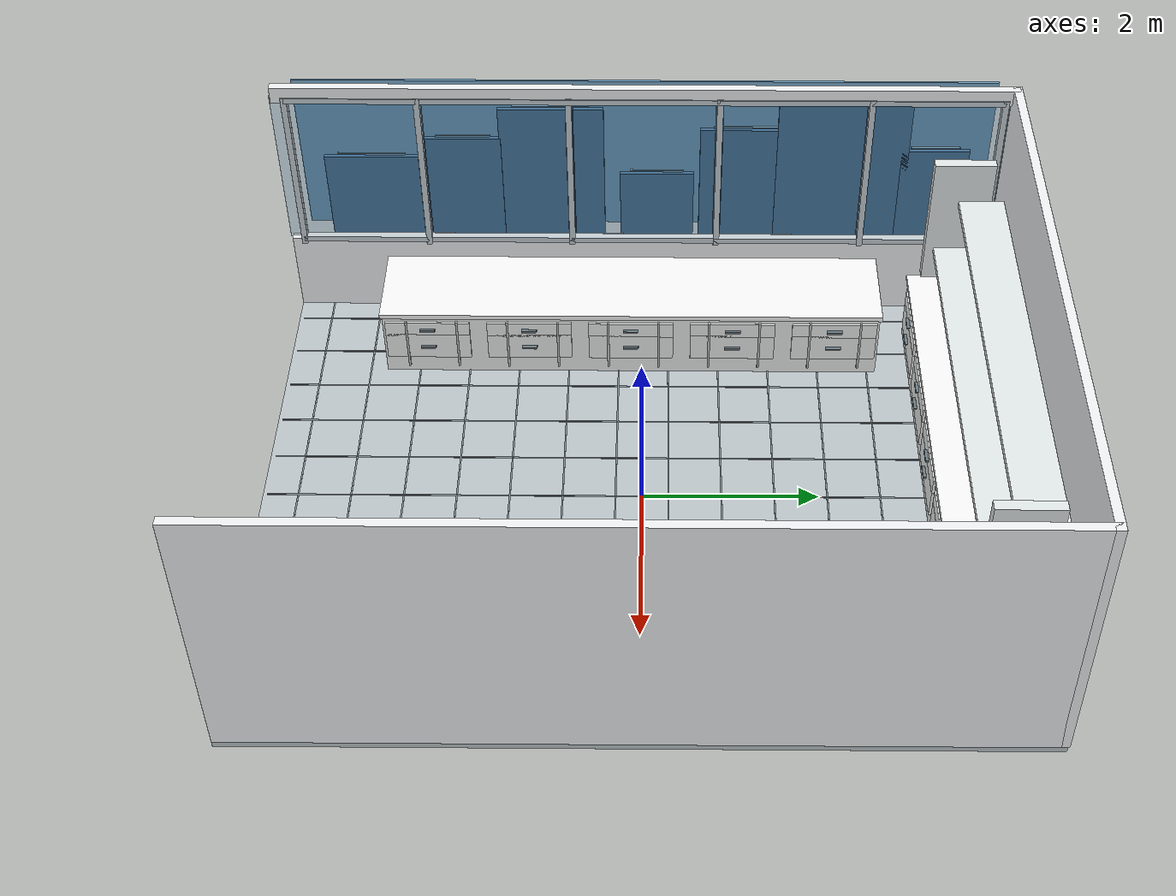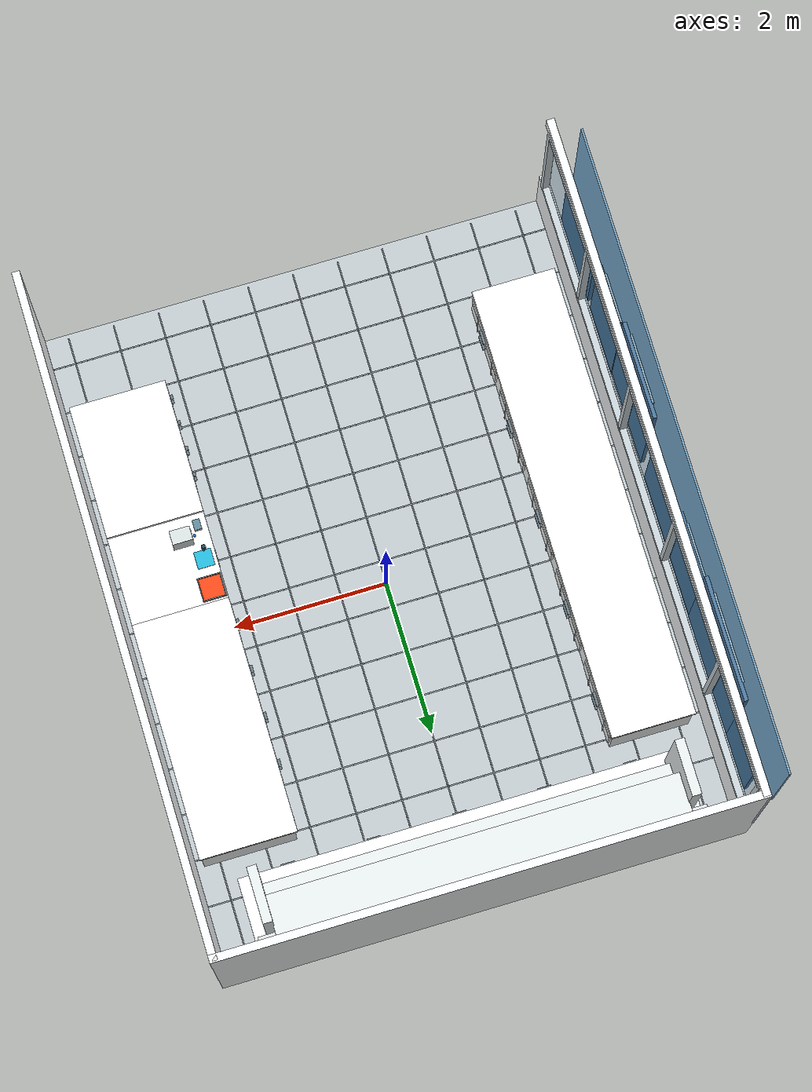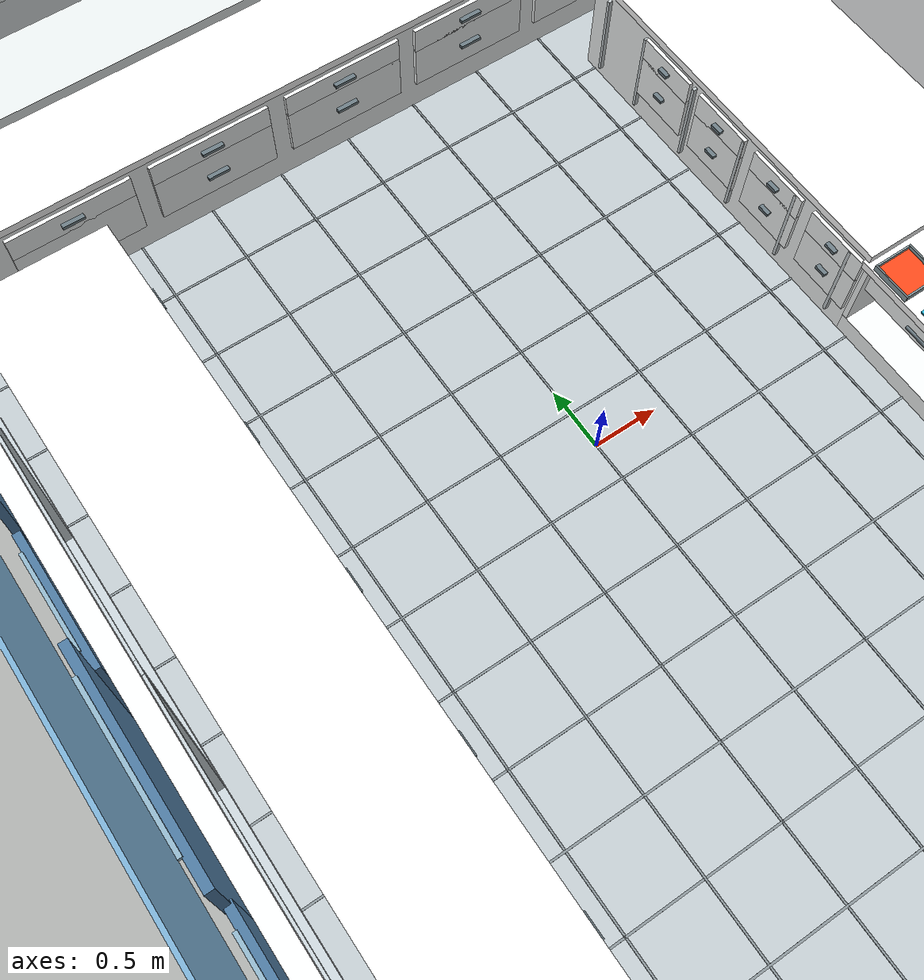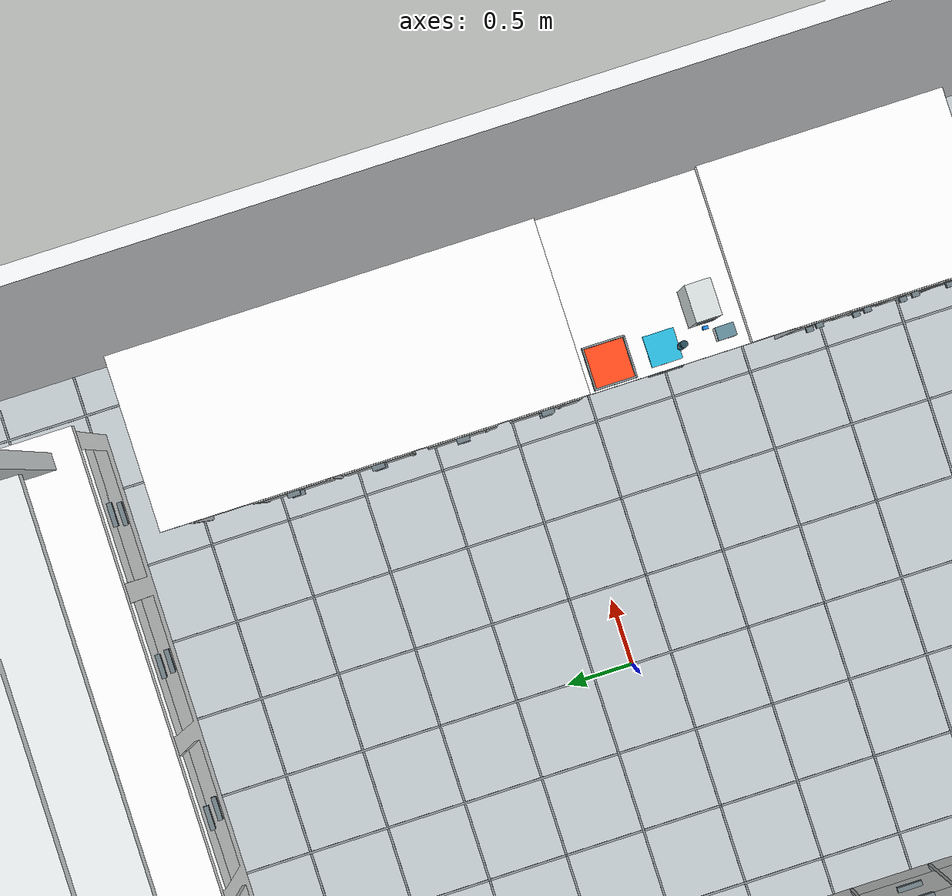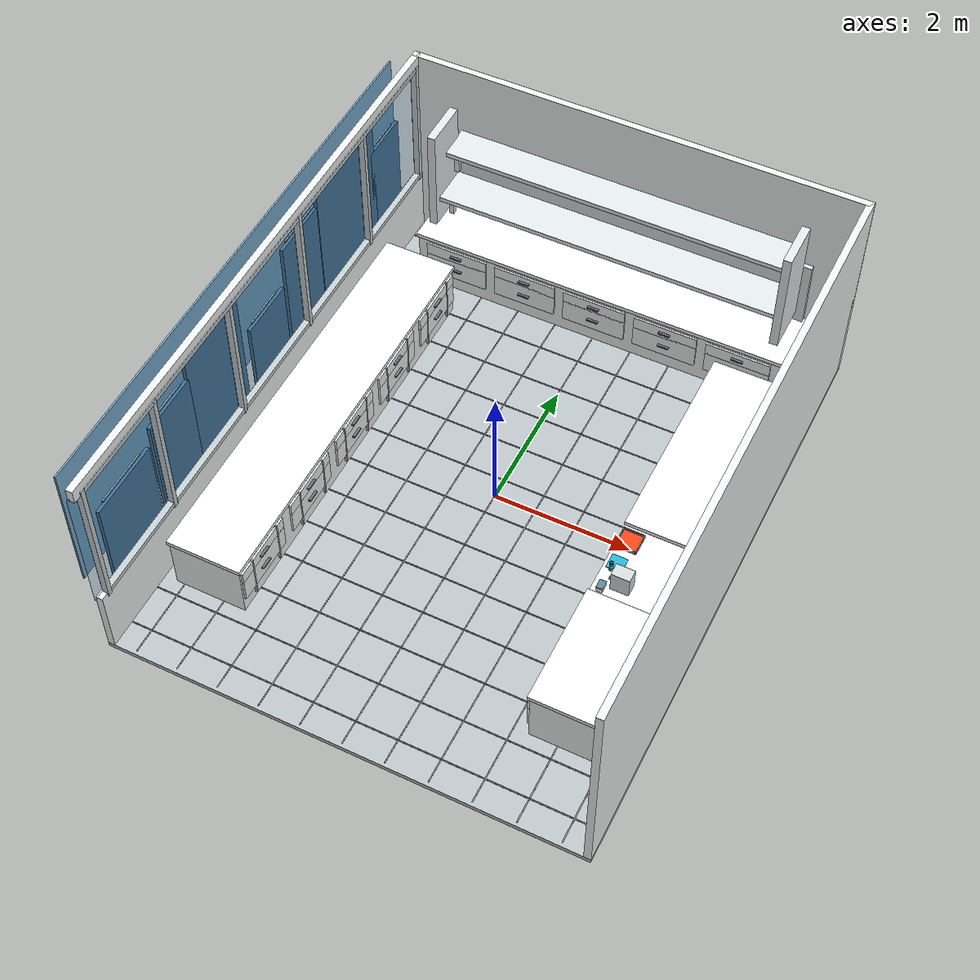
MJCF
<mujoco model="reference_laboratory">
  <asset>
    <texture name="lab_floor_checker" type="2d" builtin="checker" width="256" height="256" rgb1="0.78 0.81 0.83" rgb2="0.91 0.92 0.92" />
    <texture name="lab_glass_tint" type="2d" builtin="flat" width="256" height="256" rgb1="0.50 0.72 0.84" rgb2="0.62 0.82 0.90" />
    <texture name="lab_skybox" type="skybox" builtin="gradient" width="512" height="512" rgb1="0.91 0.94 0.97" rgb2="0.57 0.70 0.82" />
    <material name="lab_floor" rgba="0.88 0.90 0.91 1" emission="0" reflectance="0.12" shininess="0.4" specular="0.38" metallic="0" roughness="0.42" texture="lab_floor_checker" />
    <material name="lab_floor_joint" rgba="0.53 0.57 0.59 1" emission="0" reflectance="0.05" shininess="0.2" specular="0.2" metallic="0" roughness="0.68" />
    <material name="lab_wall" rgba="0.95 0.96 0.965 1" emission="0" reflectance="0.06" shininess="0.25" specular="0.25" metallic="0" roughness="0.6" />
    <material name="lab_ceiling" rgba="0.91 0.93 0.94 1" emission=".15" reflectance="0.04" shininess="0.2" specular="0.25" metallic="0" roughness="0.65" />
    <material name="lab_ceiling_grid" rgba="0.67 0.71 0.73 1" emission="0" reflectance="0.05" shininess="0.25" specular="0.25" metallic="0" roughness="0.5" />
    <material name="lab_ceiling_light" rgba="0.97 0.99 1.0 1" emission="0.72" reflectance="0.08" shininess="0.42" specular="0.35" metallic="0" roughness="0.32" />
    <material name="lab_cabinet" rgba="0.94 0.95 0.95 1" emission="0" reflectance="0.08" shininess="0.28" specular="0.32" metallic="0" roughness="0.46" />
    <material name="lab_counter" rgba="0.985 0.988 0.985 1" emission="0" reflectance="0.14" shininess="0.5" specular="0.48" metallic="0" roughness="0.28" />
    <material name="lab_cabinet_shadow" rgba="0.75 0.78 0.79 1" emission="0" reflectance="0.04" shininess="0.15" specular="0.15" metallic="0" roughness="0.75" />
    <material name="lab_toe_kick" rgba="0.38 0.43 0.45 1" emission="0" reflectance="0.1" shininess="0.24" specular="0.28" metallic="0" roughness="0.55" />
    <material name="lab_splash" rgba="0.86 0.89 0.90 1" emission="0" reflectance="0.08" shininess="0.32" specular="0.28" metallic="0" roughness="0.48" />
    <material name="lab_shelf" rgba="0.90 0.92 0.92 1" emission="0" reflectance="0.08" shininess="0.28" specular="0.28" metallic="0" roughness="0.5" />
    <material name="lab_window_frame" rgba="0.78 0.82 0.84 1" emission="0" reflectance="0.14" shininess="0.45" specular="0.42" metallic="0.15" roughness="0.33" />
    <material name="lab_glass_window" rgba="0.50 0.75 0.88 0.24" emission="0" reflectance="0.18" shininess="0.72" specular="0.82" metallic="0" roughness="0.12" texture="lab_glass_tint" />
    <material name="lab_sky" rgba="0.48 0.68 0.82 1" emission=".6" reflectance="0.02" shininess="0.15" specular="0.1" metallic="0" roughness="0.84" />
    <material name="lab_city_blue" rgba="0.30 0.47 0.62 1" emission=".15" reflectance="0.04" shininess="0.2" specular="0.17" metallic="0" roughness="0.72" />
    <material name="lab_city_light" rgba="0.56 0.70 0.78 1" emission=".15" reflectance="0.05" shininess="0.22" specular="0.2" metallic="0" roughness="0.62" />
    <material name="lab_metal" rgba="0.42 0.48 0.51 1" emission="0" reflectance="0.18" shininess="0.64" specular="0.66" metallic="0.65" roughness="0.22" />
    <material name="lab_metal_light" rgba="0.72 0.77 0.78 1" emission="0" reflectance="0.18" shininess="0.52" specular="0.58" metallic="0.4" roughness="0.28" />
    <material name="lab_metal_dark" rgba="0.16 0.20 0.22 1" emission="0" reflectance="0.22" shininess="0.56" specular="0.52" metallic="0.55" roughness="0.25" />
    <material name="lab_appliance" rgba="0.84 0.87 0.87 1" emission="0" reflectance="0.12" shininess="0.45" specular="0.42" metallic="0" roughness="0.34" />
    <material name="lab_lid" rgba="0.38 0.54 0.60 1" emission="0" reflectance="0.2" shininess="0.58" specular="0.6" metallic="0" roughness="0.22" />
    <material name="lab_well" rgba="0.08 0.12 0.14 1" emission="0" reflectance="0.05" shininess="0.25" specular="0.2" metallic="0" roughness="0.6" />
    <material name="lab_glass" rgba="0.68 0.82 0.85 0.60" emission="0" reflectance="0.2" shininess="0.72" specular="0.76" metallic="0" roughness="0.12" />
    <material name="lab_cap" rgba="0.15 0.28 0.33 1" emission="0" reflectance="0.08" shininess="0.34" specular="0.34" metallic="0" roughness="0.44" />
    <material name="lab_liquid_blue" rgba="0.12 0.54 0.70 0.92" emission="0" reflectance="0.1" shininess="0.46" specular="0.46" metallic="0" roughness="0.24" />
    <material name="lab_liquid_amber" rgba="0.76 0.46 0.12 0.92" emission="0" reflectance="0.1" shininess="0.42" specular="0.44" metallic="0" roughness="0.28" />
    <material name="lab_liquid_clear" rgba="0.74 0.88 0.88 0.72" emission="0" reflectance="0.16" shininess="0.62" specular="0.65" metallic="0" roughness="0.18" />
    <material name="lab_monitor_frame" rgba="0.27 0.31 0.33 1" emission="0" reflectance="0.12" shininess="0.44" specular="0.45" metallic="0" roughness="0.32" />
    <material name="lab_screen" rgba="0.025 0.065 0.085 1" emission="0" reflectance="0.1" shininess="0.66" specular="0.72" metallic="0" roughness="0.16" />
    <material name="lab_keyboard" rgba="0.68 0.72 0.73 1" emission="0" reflectance="0.08" shininess="0.3" specular="0.3" metallic="0" roughness="0.45" />
    <material name="lab_black" rgba="0.025 0.03 0.032 1" emission="0" reflectance="0.08" shininess="0.28" specular="0.3" metallic="0" roughness="0.5" />
    <material name="lab_lens" rgba="0.05 0.24 0.32 1" emission="0" reflectance="0.2" shininess="0.72" specular="0.78" metallic="0" roughness="0.1" />
    <material name="lab_pipette" rgba="0.95 0.96 0.94 1" emission="0" reflectance="0.08" shininess="0.4" specular="0.4" metallic="0" roughness="0.34" />
    <material name="lab_pipette_tip" rgba="0.28 0.63 0.70 0.9" emission="0" reflectance="0.12" shininess="0.48" specular="0.46" metallic="0" roughness="0.24" />
    <material name="lab_tray" rgba="0.54 0.61 0.63 1" emission="0" reflectance="0.14" shininess="0.48" specular="0.48" metallic="0.2" roughness="0.3" />
    <material name="lab_led_blue" rgba="0.08 0.54 0.95 1" emission="0.35" reflectance="0.08" shininess="0.55" specular="0.5" metallic="0" roughness="0.22" />
    <material name="lab_stool_gray" rgba="0.31 0.36 0.39 1" emission="0" reflectance="0.08" shininess="0.24" specular="0.24" metallic="0" roughness="0.64" />
    <material name="lab_caster" rgba="0.08 0.10 0.11 1" emission="0" reflectance="0.05" shininess="0.24" specular="0.22" metallic="0" roughness="0.62" />
    <material name="lab_target" rgba="0.96 0.20 0.08 0.86" emission="0.08" reflectance="0.08" shininess="0.32" specular="0.3" metallic="0" roughness="0.44" />
  </asset>
  <visual>
    <headlight ambient=".48 .48 .48" diffuse=".40 .40 .40" specular=".06 .06 .06" />
    <global offwidth="1920" offheight="1200" />
  </visual>
  <worldbody>
    <geom name="lab_floor_slab" type="box" pos="0 0 -0.035" contype="1" conaffinity="1" group="0" size="3.4 4.3 0.035" material="lab_floor" />
    <geom name="lab_back_wall" type="box" pos="0 4.27 1.625" contype="1" conaffinity="1" group="0" size="3.4 0.05 1.625" material="lab_wall" />
    <geom name="lab_right_wall" type="box" pos="3.35 0 1.625" contype="1" conaffinity="1" group="0" size="0.05 4.3 1.625" material="lab_wall" />
    <geom name="lab_left_window_sill" type="box" pos="-3.35 0 0.52" contype="1" conaffinity="1" group="0" size="0.05 4.3 0.52" material="lab_wall" />
    <geom name="lab_left_window_header" type="box" pos="-3.35 0 3.15" contype="1" conaffinity="1" group="0" size="0.05 4.3 0.1" material="lab_wall" />
    <geom name="lab_window_sky" type="box" pos="-3.7 0 2.06" contype="0" conaffinity="0" group="1" size="0.012 4.12 1.04" material="lab_sky" />
    <geom name="lab_skyline_building_0" type="box" pos="-3.49 -3.25 1.34" contype="0" conaffinity="0" group="1" size="0.025 0.56 0.82" material="lab_city_blue" />
    <geom name="lab_skyline_roof_0" type="box" pos="-3.52 -3.25 2.16" contype="0" conaffinity="0" group="1" size="0.012 0.4032 0.018" material="lab_city_light" />
    <geom name="lab_skyline_building_1" type="box" pos="-3.5 -2.15 1.47" contype="0" conaffinity="0" group="1" size="0.025 0.45 0.95" material="lab_city_blue" />
    <geom name="lab_skyline_roof_1" type="box" pos="-3.53 -2.15 2.42" contype="0" conaffinity="0" group="1" size="0.012 0.324 0.018" material="lab_city_light" />
    <geom name="lab_skyline_building_2" type="box" pos="-3.51 -1.1 1.68" contype="0" conaffinity="0" group="1" size="0.025 0.62 1.16" material="lab_city_blue" />
    <geom name="lab_skyline_roof_2" type="box" pos="-3.54 -1.1 2.84" contype="0" conaffinity="0" group="1" size="0.012 0.4464 0.018" material="lab_city_light" />
    <geom name="lab_skyline_building_3" type="box" pos="-3.5 0.15 1.22" contype="0" conaffinity="0" group="1" size="0.025 0.44 0.7" material="lab_city_blue" />
    <geom name="lab_skyline_roof_3" type="box" pos="-3.53 0.15 1.92" contype="0" conaffinity="0" group="1" size="0.012 0.3168 0.018" material="lab_city_light" />
    <geom name="lab_skyline_building_4" type="box" pos="-3.5 1.22 1.54" contype="0" conaffinity="0" group="1" size="0.025 0.56 1.02" material="lab_city_blue" />
    <geom name="lab_skyline_roof_4" type="box" pos="-3.53 1.22 2.56" contype="0" conaffinity="0" group="1" size="0.012 0.4032 0.018" material="lab_city_light" />
    <geom name="lab_skyline_building_5" type="box" pos="-3.49 2.35 1.76" contype="0" conaffinity="0" group="1" size="0.025 0.78 1.24" material="lab_city_blue" />
    <geom name="lab_skyline_roof_5" type="box" pos="-3.52 2.35 3" contype="0" conaffinity="0" group="1" size="0.012 0.5616 0.018" material="lab_city_light" />
    <geom name="lab_skyline_building_6" type="box" pos="-3.49 3.45 1.4" contype="0" conaffinity="0" group="1" size="0.025 0.4 0.88" material="lab_city_blue" />
    <geom name="lab_skyline_roof_6" type="box" pos="-3.52 3.45 2.28" contype="0" conaffinity="0" group="1" size="0.012 0.288 0.018" material="lab_city_light" />
    <geom name="lab_window_glass_0" type="box" pos="-3.385 -3.5 2.05" contype="0" conaffinity="0" group="1" size="0.012 0.83 1.03" material="lab_glass_window" />
    <geom name="lab_window_glass_1" type="box" pos="-3.385 -1.75 2.05" contype="0" conaffinity="0" group="1" size="0.012 0.83 1.03" material="lab_glass_window" />
    <geom name="lab_window_glass_2" type="box" pos="-3.385 0 2.05" contype="0" conaffinity="0" group="1" size="0.012 0.83 1.03" material="lab_glass_window" />
    <geom name="lab_window_glass_3" type="box" pos="-3.385 1.75 2.05" contype="0" conaffinity="0" group="1" size="0.012 0.83 1.03" material="lab_glass_window" />
    <geom name="lab_window_glass_4" type="box" pos="-3.385 3.5 2.05" contype="0" conaffinity="0" group="1" size="0.012 0.83 1.03" material="lab_glass_window" />
    <geom name="lab_window_mullion_0" type="box" pos="-3.33 -4.15 2.05" contype="0" conaffinity="0" group="2" size="0.045 0.035 1.07" material="lab_window_frame" />
    <geom name="lab_window_mullion_1" type="box" pos="-3.33 -2.625 2.05" contype="0" conaffinity="0" group="2" size="0.045 0.035 1.07" material="lab_window_frame" />
    <geom name="lab_window_mullion_2" type="box" pos="-3.33 -0.875 2.05" contype="0" conaffinity="0" group="2" size="0.045 0.035 1.07" material="lab_window_frame" />
    <geom name="lab_window_mullion_3" type="box" pos="-3.33 0.875 2.05" contype="0" conaffinity="0" group="2" size="0.045 0.035 1.07" material="lab_window_frame" />
    <geom name="lab_window_mullion_4" type="box" pos="-3.33 2.625 2.05" contype="0" conaffinity="0" group="2" size="0.045 0.035 1.07" material="lab_window_frame" />
    <geom name="lab_window_mullion_5" type="box" pos="-3.33 4.15 2.05" contype="0" conaffinity="0" group="2" size="0.045 0.035 1.07" material="lab_window_frame" />
    <geom name="lab_window_transom" type="box" pos="-3.33 0 1.05" contype="0" conaffinity="0" group="2" size="0.045 4.15 0.035" material="lab_window_frame" />
    <geom name="lab_window_top_rail" type="box" pos="-3.33 0 3.08" contype="0" conaffinity="0" group="2" size="0.045 4.15 0.035" material="lab_window_frame" />
    <geom name="lab_floor_joint_x_0" type="box" pos="-3 0 0.002" contype="0" conaffinity="0" group="1" size="0.008 4.25 0.002" material="lab_floor_joint" />
    <geom name="lab_floor_joint_x_1" type="box" pos="-2.4 0 0.002" contype="0" conaffinity="0" group="1" size="0.008 4.25 0.002" material="lab_floor_joint" />
    <geom name="lab_floor_joint_x_2" type="box" pos="-1.8 0 0.002" contype="0" conaffinity="0" group="1" size="0.008 4.25 0.002" material="lab_floor_joint" />
    <geom name="lab_floor_joint_x_3" type="box" pos="-1.2 0 0.002" contype="0" conaffinity="0" group="1" size="0.008 4.25 0.002" material="lab_floor_joint" />
    <geom name="lab_floor_joint_x_4" type="box" pos="-0.6 0 0.002" contype="0" conaffinity="0" group="1" size="0.008 4.25 0.002" material="lab_floor_joint" />
    <geom name="lab_floor_joint_x_5" type="box" pos="0 0 0.002" contype="0" conaffinity="0" group="1" size="0.008 4.25 0.002" material="lab_floor_joint" />
    <geom name="lab_floor_joint_x_6" type="box" pos="0.6 0 0.002" contype="0" conaffinity="0" group="1" size="0.008 4.25 0.002" material="lab_floor_joint" />
    <geom name="lab_floor_joint_x_7" type="box" pos="1.2 0 0.002" contype="0" conaffinity="0" group="1" size="0.008 4.25 0.002" material="lab_floor_joint" />
    <geom name="lab_floor_joint_x_8" type="box" pos="1.8 0 0.002" contype="0" conaffinity="0" group="1" size="0.008 4.25 0.002" material="lab_floor_joint" />
    <geom name="lab_floor_joint_x_9" type="box" pos="2.4 0 0.002" contype="0" conaffinity="0" group="1" size="0.008 4.25 0.002" material="lab_floor_joint" />
    <geom name="lab_floor_joint_x_10" type="box" pos="3 0 0.002" contype="0" conaffinity="0" group="1" size="0.008 4.25 0.002" material="lab_floor_joint" />
    <geom name="lab_floor_joint_y_0" type="box" pos="0 -3.9 0.002" contype="0" conaffinity="0" group="1" size="3.35 0.008 0.002" material="lab_floor_joint" />
    <geom name="lab_floor_joint_y_1" type="box" pos="0 -3.3 0.002" contype="0" conaffinity="0" group="1" size="3.35 0.008 0.002" material="lab_floor_joint" />
    <geom name="lab_floor_joint_y_2" type="box" pos="0 -2.7 0.002" contype="0" conaffinity="0" group="1" size="3.35 0.008 0.002" material="lab_floor_joint" />
    <geom name="lab_floor_joint_y_3" type="box" pos="0 -2.1 0.002" contype="0" conaffinity="0" group="1" size="3.35 0.008 0.002" material="lab_floor_joint" />
    <geom name="lab_floor_joint_y_4" type="box" pos="0 -1.5 0.002" contype="0" conaffinity="0" group="1" size="3.35 0.008 0.002" material="lab_floor_joint" />
    <geom name="lab_floor_joint_y_5" type="box" pos="0 -0.9 0.002" contype="0" conaffinity="0" group="1" size="3.35 0.008 0.002" material="lab_floor_joint" />
    <geom name="lab_floor_joint_y_6" type="box" pos="0 -0.3 0.002" contype="0" conaffinity="0" group="1" size="3.35 0.008 0.002" material="lab_floor_joint" />
    <geom name="lab_floor_joint_y_7" type="box" pos="0 0.3 0.002" contype="0" conaffinity="0" group="1" size="3.35 0.008 0.002" material="lab_floor_joint" />
    <geom name="lab_floor_joint_y_8" type="box" pos="0 0.9 0.002" contype="0" conaffinity="0" group="1" size="3.35 0.008 0.002" material="lab_floor_joint" />
    <geom name="lab_floor_joint_y_9" type="box" pos="0 1.5 0.002" contype="0" conaffinity="0" group="1" size="3.35 0.008 0.002" material="lab_floor_joint" />
    <geom name="lab_floor_joint_y_10" type="box" pos="0 2.1 0.002" contype="0" conaffinity="0" group="1" size="3.35 0.008 0.002" material="lab_floor_joint" />
    <geom name="lab_floor_joint_y_11" type="box" pos="0 2.7 0.002" contype="0" conaffinity="0" group="1" size="3.35 0.008 0.002" material="lab_floor_joint" />
    <geom name="lab_floor_joint_y_12" type="box" pos="0 3.3 0.002" contype="0" conaffinity="0" group="1" size="3.35 0.008 0.002" material="lab_floor_joint" />
    <geom name="lab_floor_joint_y_13" type="box" pos="0 3.9 0.002" contype="0" conaffinity="0" group="1" size="3.35 0.008 0.002" material="lab_floor_joint" />
    <geom name="lab_ceiling_slab" type="box" pos="0 0 3.22" contype="0" conaffinity="0" group="5" size="3.4 4.3 0.03" material="lab_ceiling" />
    <geom name="lab_ceiling_grid_x_0" type="box" pos="-3 0 3.175" contype="0" conaffinity="0" group="5" size="0.018 4.24 0.018" material="lab_ceiling_grid" />
    <geom name="lab_ceiling_grid_x_1" type="box" pos="-2.4 0 3.175" contype="0" conaffinity="0" group="5" size="0.018 4.24 0.018" material="lab_ceiling_grid" />
    <geom name="lab_ceiling_grid_x_2" type="box" pos="-1.8 0 3.175" contype="0" conaffinity="0" group="5" size="0.018 4.24 0.018" material="lab_ceiling_grid" />
    <geom name="lab_ceiling_grid_x_3" type="box" pos="-1.2 0 3.175" contype="0" conaffinity="0" group="5" size="0.018 4.24 0.018" material="lab_ceiling_grid" />
    <geom name="lab_ceiling_grid_x_4" type="box" pos="-0.6 0 3.175" contype="0" conaffinity="0" group="5" size="0.018 4.24 0.018" material="lab_ceiling_grid" />
    <geom name="lab_ceiling_grid_x_5" type="box" pos="0 0 3.175" contype="0" conaffinity="0" group="5" size="0.018 4.24 0.018" material="lab_ceiling_grid" />
    <geom name="lab_ceiling_grid_x_6" type="box" pos="0.6 0 3.175" contype="0" conaffinity="0" group="5" size="0.018 4.24 0.018" material="lab_ceiling_grid" />
    <geom name="lab_ceiling_grid_x_7" type="box" pos="1.2 0 3.175" contype="0" conaffinity="0" group="5" size="0.018 4.24 0.018" material="lab_ceiling_grid" />
    <geom name="lab_ceiling_grid_x_8" type="box" pos="1.8 0 3.175" contype="0" conaffinity="0" group="5" size="0.018 4.24 0.018" material="lab_ceiling_grid" />
    <geom name="lab_ceiling_grid_x_9" type="box" pos="2.4 0 3.175" contype="0" conaffinity="0" group="5" size="0.018 4.24 0.018" material="lab_ceiling_grid" />
    <geom name="lab_ceiling_grid_x_10" type="box" pos="3 0 3.175" contype="0" conaffinity="0" group="5" size="0.018 4.24 0.018" material="lab_ceiling_grid" />
    <geom name="lab_ceiling_grid_y_0" type="box" pos="0 -3.9 3.175" contype="0" conaffinity="0" group="5" size="3.35 0.018 0.018" material="lab_ceiling_grid" />
    <geom name="lab_ceiling_grid_y_1" type="box" pos="0 -3.3 3.175" contype="0" conaffinity="0" group="5" size="3.35 0.018 0.018" material="lab_ceiling_grid" />
    <geom name="lab_ceiling_grid_y_2" type="box" pos="0 -2.7 3.175" contype="0" conaffinity="0" group="5" size="3.35 0.018 0.018" material="lab_ceiling_grid" />
    <geom name="lab_ceiling_grid_y_3" type="box" pos="0 -2.1 3.175" contype="0" conaffinity="0" group="5" size="3.35 0.018 0.018" material="lab_ceiling_grid" />
    <geom name="lab_ceiling_grid_y_4" type="box" pos="0 -1.5 3.175" contype="0" conaffinity="0" group="5" size="3.35 0.018 0.018" material="lab_ceiling_grid" />
    <geom name="lab_ceiling_grid_y_5" type="box" pos="0 -0.9 3.175" contype="0" conaffinity="0" group="5" size="3.35 0.018 0.018" material="lab_ceiling_grid" />
    <geom name="lab_ceiling_grid_y_6" type="box" pos="0 -0.3 3.175" contype="0" conaffinity="0" group="5" size="3.35 0.018 0.018" material="lab_ceiling_grid" />
    <geom name="lab_ceiling_grid_y_7" type="box" pos="0 0.3 3.175" contype="0" conaffinity="0" group="5" size="3.35 0.018 0.018" material="lab_ceiling_grid" />
    <geom name="lab_ceiling_grid_y_8" type="box" pos="0 0.9 3.175" contype="0" conaffinity="0" group="5" size="3.35 0.018 0.018" material="lab_ceiling_grid" />
    <geom name="lab_ceiling_grid_y_9" type="box" pos="0 1.5 3.175" contype="0" conaffinity="0" group="5" size="3.35 0.018 0.018" material="lab_ceiling_grid" />
    <geom name="lab_ceiling_grid_y_10" type="box" pos="0 2.1 3.175" contype="0" conaffinity="0" group="5" size="3.35 0.018 0.018" material="lab_ceiling_grid" />
    <geom name="lab_ceiling_grid_y_11" type="box" pos="0 2.7 3.175" contype="0" conaffinity="0" group="5" size="3.35 0.018 0.018" material="lab_ceiling_grid" />
    <geom name="lab_ceiling_grid_y_12" type="box" pos="0 3.3 3.175" contype="0" conaffinity="0" group="5" size="3.35 0.018 0.018" material="lab_ceiling_grid" />
    <geom name="lab_ceiling_grid_y_13" type="box" pos="0 3.9 3.175" contype="0" conaffinity="0" group="5" size="3.35 0.018 0.018" material="lab_ceiling_grid" />
    <geom name="lab_ceiling_panel_0" type="box" pos="-2.35 -2.85 3.145" contype="0" conaffinity="0" group="5" size="0.36 0.24 0.012" material="lab_ceiling_light" />
    <geom name="lab_ceiling_panel_1" type="box" pos="-0.75 -2.85 3.145" contype="0" conaffinity="0" group="5" size="0.36 0.24 0.012" material="lab_ceiling_light" />
    <geom name="lab_ceiling_panel_2" type="box" pos="0.85 -2.85 3.145" contype="0" conaffinity="0" group="5" size="0.36 0.24 0.012" material="lab_ceiling_light" />
    <geom name="lab_ceiling_panel_3" type="box" pos="2.45 -2.85 3.145" contype="0" conaffinity="0" group="5" size="0.36 0.24 0.012" material="lab_ceiling_light" />
    <geom name="lab_ceiling_panel_4" type="box" pos="-1.55 -0.95 3.145" contype="0" conaffinity="0" group="5" size="0.36 0.24 0.012" material="lab_ceiling_light" />
    <geom name="lab_ceiling_panel_5" type="box" pos="0.05 -0.95 3.145" contype="0" conaffinity="0" group="5" size="0.36 0.24 0.012" material="lab_ceiling_light" />
    <geom name="lab_ceiling_panel_6" type="box" pos="1.65 -0.95 3.145" contype="0" conaffinity="0" group="5" size="0.36 0.24 0.012" material="lab_ceiling_light" />
    <geom name="lab_ceiling_panel_7" type="box" pos="-2.35 1.05 3.145" contype="0" conaffinity="0" group="5" size="0.36 0.24 0.012" material="lab_ceiling_light" />
    <geom name="lab_ceiling_panel_8" type="box" pos="-0.75 1.05 3.145" contype="0" conaffinity="0" group="5" size="0.36 0.24 0.012" material="lab_ceiling_light" />
    <geom name="lab_ceiling_panel_9" type="box" pos="0.85 1.05 3.145" contype="0" conaffinity="0" group="5" size="0.36 0.24 0.012" material="lab_ceiling_light" />
    <geom name="lab_ceiling_panel_10" type="box" pos="2.45 1.05 3.145" contype="0" conaffinity="0" group="5" size="0.36 0.24 0.012" material="lab_ceiling_light" />
    <geom name="lab_ceiling_panel_11" type="box" pos="-1.55 2.95 3.145" contype="0" conaffinity="0" group="5" size="0.36 0.24 0.012" material="lab_ceiling_light" />
    <geom name="lab_ceiling_panel_12" type="box" pos="0.05 2.95 3.145" contype="0" conaffinity="0" group="5" size="0.36 0.24 0.012" material="lab_ceiling_light" />
    <geom name="lab_ceiling_panel_13" type="box" pos="1.65 2.95 3.145" contype="0" conaffinity="0" group="5" size="0.36 0.24 0.012" material="lab_ceiling_light" />
    <geom name="lab_left_bench_body" type="box" pos="-2.6 -0.15 0.42" contype="1" conaffinity="1" group="0" size="0.52 2.95 0.42" material="lab_cabinet" />
    <geom name="lab_left_bench_counter" type="box" pos="-2.6 -0.15 0.87" contype="1" conaffinity="1" group="0" size="0.545 2.975 0.03" material="lab_counter" />
    <geom name="lab_left_bench_drawer_0_panel" type="box" pos="-2.068 -2.569 0.42" contype="0" conaffinity="0" group="2" size="0.018 0.5015 0.18" material="lab_cabinet" />
    <geom name="lab_left_bench_drawer_0_handle" type="box" pos="-2.032 -2.569 0.42" contype="0" conaffinity="0" group="2" size="0.018 0.09027 0.012" material="lab_metal" />
    <geom name="lab_left_bench_drawer_low_0_panel" type="box" pos="-2.068 -2.569 0.68" contype="0" conaffinity="0" group="2" size="0.018 0.5015 0.1" material="lab_cabinet" />
    <geom name="lab_left_bench_drawer_low_0_handle" type="box" pos="-2.032 -2.569 0.68" contype="0" conaffinity="0" group="2" size="0.018 0.09027 0.012" material="lab_metal" />
    <geom name="lab_left_bench_drawer_1_panel" type="box" pos="-2.068 -1.3595 0.42" contype="0" conaffinity="0" group="2" size="0.018 0.5015 0.18" material="lab_cabinet" />
    <geom name="lab_left_bench_drawer_1_handle" type="box" pos="-2.032 -1.3595 0.42" contype="0" conaffinity="0" group="2" size="0.018 0.09027 0.012" material="lab_metal" />
    <geom name="lab_left_bench_drawer_low_1_panel" type="box" pos="-2.068 -1.3595 0.68" contype="0" conaffinity="0" group="2" size="0.018 0.5015 0.1" material="lab_cabinet" />
    <geom name="lab_left_bench_drawer_low_1_handle" type="box" pos="-2.032 -1.3595 0.68" contype="0" conaffinity="0" group="2" size="0.018 0.09027 0.012" material="lab_metal" />
    <geom name="lab_left_bench_drawer_2_panel" type="box" pos="-2.068 -0.15 0.42" contype="0" conaffinity="0" group="2" size="0.018 0.5015 0.18" material="lab_cabinet" />
    <geom name="lab_left_bench_drawer_2_handle" type="box" pos="-2.032 -0.15 0.42" contype="0" conaffinity="0" group="2" size="0.018 0.09027 0.012" material="lab_metal" />
    <geom name="lab_left_bench_drawer_low_2_panel" type="box" pos="-2.068 -0.15 0.68" contype="0" conaffinity="0" group="2" size="0.018 0.5015 0.1" material="lab_cabinet" />
    <geom name="lab_left_bench_drawer_low_2_handle" type="box" pos="-2.032 -0.15 0.68" contype="0" conaffinity="0" group="2" size="0.018 0.09027 0.012" material="lab_metal" />
    <geom name="lab_left_bench_drawer_3_panel" type="box" pos="-2.068 1.0595 0.42" contype="0" conaffinity="0" group="2" size="0.018 0.5015 0.18" material="lab_cabinet" />
    <geom name="lab_left_bench_drawer_3_handle" type="box" pos="-2.032 1.0595 0.42" contype="0" conaffinity="0" group="2" size="0.018 0.09027 0.012" material="lab_metal" />
    <geom name="lab_left_bench_drawer_low_3_panel" type="box" pos="-2.068 1.0595 0.68" contype="0" conaffinity="0" group="2" size="0.018 0.5015 0.1" material="lab_cabinet" />
    <geom name="lab_left_bench_drawer_low_3_handle" type="box" pos="-2.032 1.0595 0.68" contype="0" conaffinity="0" group="2" size="0.018 0.09027 0.012" material="lab_metal" />
    <geom name="lab_left_bench_drawer_4_panel" type="box" pos="-2.068 2.269 0.42" contype="0" conaffinity="0" group="2" size="0.018 0.5015 0.18" material="lab_cabinet" />
    <geom name="lab_left_bench_drawer_4_handle" type="box" pos="-2.032 2.269 0.42" contype="0" conaffinity="0" group="2" size="0.018 0.09027 0.012" material="lab_metal" />
    <geom name="lab_left_bench_drawer_low_4_panel" type="box" pos="-2.068 2.269 0.68" contype="0" conaffinity="0" group="2" size="0.018 0.5015 0.1" material="lab_cabinet" />
    <geom name="lab_left_bench_drawer_low_4_handle" type="box" pos="-2.032 2.269 0.68" contype="0" conaffinity="0" group="2" size="0.018 0.09027 0.012" material="lab_metal" />
    <geom name="lab_right_front_body" type="box" pos="2.6 -2.25 0.42" contype="1" conaffinity="1" group="0" size="0.6 0.85 0.42" material="lab_cabinet" />
    <geom name="lab_right_front_counter" type="box" pos="2.6 -2.25 0.87" contype="1" conaffinity="1" group="0" size="0.625 0.875 0.03" material="lab_counter" />
    <geom name="lab_right_front_drawer_0_panel" type="box" pos="1.988 -2.947 0.42" contype="0" conaffinity="0" group="2" size="0.018 0.1445 0.18" material="lab_cabinet" />
    <geom name="lab_right_front_drawer_0_handle" type="box" pos="1.952 -2.947 0.42" contype="0" conaffinity="0" group="2" size="0.018 0.02601 0.012" material="lab_metal" />
    <geom name="lab_right_front_drawer_low_0_panel" type="box" pos="1.988 -2.947 0.68" contype="0" conaffinity="0" group="2" size="0.018 0.1445 0.1" material="lab_cabinet" />
    <geom name="lab_right_front_drawer_low_0_handle" type="box" pos="1.952 -2.947 0.68" contype="0" conaffinity="0" group="2" size="0.018 0.02601 0.012" material="lab_metal" />
    <geom name="lab_right_front_drawer_1_panel" type="box" pos="1.988 -2.5985 0.42" contype="0" conaffinity="0" group="2" size="0.018 0.1445 0.18" material="lab_cabinet" />
    <geom name="lab_right_front_drawer_1_handle" type="box" pos="1.952 -2.5985 0.42" contype="0" conaffinity="0" group="2" size="0.018 0.02601 0.012" material="lab_metal" />
    <geom name="lab_right_front_drawer_low_1_panel" type="box" pos="1.988 -2.5985 0.68" contype="0" conaffinity="0" group="2" size="0.018 0.1445 0.1" material="lab_cabinet" />
    <geom name="lab_right_front_drawer_low_1_handle" type="box" pos="1.952 -2.5985 0.68" contype="0" conaffinity="0" group="2" size="0.018 0.02601 0.012" material="lab_metal" />
    <geom name="lab_right_front_drawer_2_panel" type="box" pos="1.988 -2.25 0.42" contype="0" conaffinity="0" group="2" size="0.018 0.1445 0.18" material="lab_cabinet" />
    <geom name="lab_right_front_drawer_2_handle" type="box" pos="1.952 -2.25 0.42" contype="0" conaffinity="0" group="2" size="0.018 0.02601 0.012" material="lab_metal" />
    <geom name="lab_right_front_drawer_low_2_panel" type="box" pos="1.988 -2.25 0.68" contype="0" conaffinity="0" group="2" size="0.018 0.1445 0.1" material="lab_cabinet" />
    <geom name="lab_right_front_drawer_low_2_handle" type="box" pos="1.952 -2.25 0.68" contype="0" conaffinity="0" group="2" size="0.018 0.02601 0.012" material="lab_metal" />
    <geom name="lab_right_front_drawer_3_panel" type="box" pos="1.988 -1.9015 0.42" contype="0" conaffinity="0" group="2" size="0.018 0.1445 0.18" material="lab_cabinet" />
    <geom name="lab_right_front_drawer_3_handle" type="box" pos="1.952 -1.9015 0.42" contype="0" conaffinity="0" group="2" size="0.018 0.02601 0.012" material="lab_metal" />
    <geom name="lab_right_front_drawer_low_3_panel" type="box" pos="1.988 -1.9015 0.68" contype="0" conaffinity="0" group="2" size="0.018 0.1445 0.1" material="lab_cabinet" />
    <geom name="lab_right_front_drawer_low_3_handle" type="box" pos="1.952 -1.9015 0.68" contype="0" conaffinity="0" group="2" size="0.018 0.02601 0.012" material="lab_metal" />
    <geom name="lab_right_workstation_counter" type="box" pos="2.6 -0.8 0.77" contype="1" conaffinity="1" group="0" size="0.625 0.625 0.03" material="lab_counter" />
    <geom name="lab_right_rear_body" type="box" pos="2.6 1.3 0.42" contype="1" conaffinity="1" group="0" size="0.6 1.5 0.42" material="lab_cabinet" />
    <geom name="lab_right_rear_counter" type="box" pos="2.6 1.3 0.87" contype="1" conaffinity="1" group="0" size="0.625 1.525 0.03" material="lab_counter" />
    <geom name="lab_right_rear_drawer_0_panel" type="box" pos="1.988 0.07 0.42" contype="0" conaffinity="0" group="2" size="0.018 0.255 0.18" material="lab_cabinet" />
    <geom name="lab_right_rear_drawer_0_handle" type="box" pos="1.952 0.07 0.42" contype="0" conaffinity="0" group="2" size="0.018 0.0459 0.012" material="lab_metal" />
    <geom name="lab_right_rear_drawer_low_0_panel" type="box" pos="1.988 0.07 0.68" contype="0" conaffinity="0" group="2" size="0.018 0.255 0.1" material="lab_cabinet" />
    <geom name="lab_right_rear_drawer_low_0_handle" type="box" pos="1.952 0.07 0.68" contype="0" conaffinity="0" group="2" size="0.018 0.0459 0.012" material="lab_metal" />
    <geom name="lab_right_rear_drawer_1_panel" type="box" pos="1.988 0.685 0.42" contype="0" conaffinity="0" group="2" size="0.018 0.255 0.18" material="lab_cabinet" />
    <geom name="lab_right_rear_drawer_1_handle" type="box" pos="1.952 0.685 0.42" contype="0" conaffinity="0" group="2" size="0.018 0.0459 0.012" material="lab_metal" />
    <geom name="lab_right_rear_drawer_low_1_panel" type="box" pos="1.988 0.685 0.68" contype="0" conaffinity="0" group="2" size="0.018 0.255 0.1" material="lab_cabinet" />
    <geom name="lab_right_rear_drawer_low_1_handle" type="box" pos="1.952 0.685 0.68" contype="0" conaffinity="0" group="2" size="0.018 0.0459 0.012" material="lab_metal" />
    <geom name="lab_right_rear_drawer_2_panel" type="box" pos="1.988 1.3 0.42" contype="0" conaffinity="0" group="2" size="0.018 0.255 0.18" material="lab_cabinet" />
    <geom name="lab_right_rear_drawer_2_handle" type="box" pos="1.952 1.3 0.42" contype="0" conaffinity="0" group="2" size="0.018 0.0459 0.012" material="lab_metal" />
    <geom name="lab_right_rear_drawer_low_2_panel" type="box" pos="1.988 1.3 0.68" contype="0" conaffinity="0" group="2" size="0.018 0.255 0.1" material="lab_cabinet" />
    <geom name="lab_right_rear_drawer_low_2_handle" type="box" pos="1.952 1.3 0.68" contype="0" conaffinity="0" group="2" size="0.018 0.0459 0.012" material="lab_metal" />
    <geom name="lab_right_rear_drawer_3_panel" type="box" pos="1.988 1.915 0.42" contype="0" conaffinity="0" group="2" size="0.018 0.255 0.18" material="lab_cabinet" />
    <geom name="lab_right_rear_drawer_3_handle" type="box" pos="1.952 1.915 0.42" contype="0" conaffinity="0" group="2" size="0.018 0.0459 0.012" material="lab_metal" />
    <geom name="lab_right_rear_drawer_low_3_panel" type="box" pos="1.988 1.915 0.68" contype="0" conaffinity="0" group="2" size="0.018 0.255 0.1" material="lab_cabinet" />
    <geom name="lab_right_rear_drawer_low_3_handle" type="box" pos="1.952 1.915 0.68" contype="0" conaffinity="0" group="2" size="0.018 0.0459 0.012" material="lab_metal" />
    <geom name="lab_left_inner_seam_0" type="box" pos="-2.065 -2.82 0.44" contype="0" conaffinity="0" group="2" size="0.016 0.012 0.35" material="lab_cabinet_shadow" />
    <geom name="lab_left_inner_seam_1" type="box" pos="-2.065 -2.22 0.44" contype="0" conaffinity="0" group="2" size="0.016 0.012 0.35" material="lab_cabinet_shadow" />
    <geom name="lab_left_inner_seam_2" type="box" pos="-2.065 -1.62 0.44" contype="0" conaffinity="0" group="2" size="0.016 0.012 0.35" material="lab_cabinet_shadow" />
    <geom name="lab_left_inner_seam_3" type="box" pos="-2.065 -1.02 0.44" contype="0" conaffinity="0" group="2" size="0.016 0.012 0.35" material="lab_cabinet_shadow" />
    <geom name="lab_left_inner_seam_4" type="box" pos="-2.065 -0.42 0.44" contype="0" conaffinity="0" group="2" size="0.016 0.012 0.35" material="lab_cabinet_shadow" />
    <geom name="lab_left_inner_seam_5" type="box" pos="-2.065 0.18 0.44" contype="0" conaffinity="0" group="2" size="0.016 0.012 0.35" material="lab_cabinet_shadow" />
    <geom name="lab_left_inner_seam_6" type="box" pos="-2.065 0.78 0.44" contype="0" conaffinity="0" group="2" size="0.016 0.012 0.35" material="lab_cabinet_shadow" />
    <geom name="lab_left_inner_seam_7" type="box" pos="-2.065 1.38 0.44" contype="0" conaffinity="0" group="2" size="0.016 0.012 0.35" material="lab_cabinet_shadow" />
    <geom name="lab_left_inner_seam_8" type="box" pos="-2.065 1.98 0.44" contype="0" conaffinity="0" group="2" size="0.016 0.012 0.35" material="lab_cabinet_shadow" />
    <geom name="lab_left_inner_seam_9" type="box" pos="-2.065 2.58 0.44" contype="0" conaffinity="0" group="2" size="0.016 0.012 0.35" material="lab_cabinet_shadow" />
    <geom name="lab_right_inner_seam_0" type="box" pos="1.985 -2.86 0.43" contype="0" conaffinity="0" group="2" size="0.016 0.012 0.34" material="lab_cabinet_shadow" />
    <geom name="lab_right_inner_seam_1" type="box" pos="1.985 -2.3 0.43" contype="0" conaffinity="0" group="2" size="0.016 0.012 0.34" material="lab_cabinet_shadow" />
    <geom name="lab_right_inner_seam_2" type="box" pos="1.985 -1.74 0.43" contype="0" conaffinity="0" group="2" size="0.016 0.012 0.34" material="lab_cabinet_shadow" />
    <geom name="lab_right_inner_seam_5" type="box" pos="1.985 -0.06 0.43" contype="0" conaffinity="0" group="2" size="0.016 0.012 0.34" material="lab_cabinet_shadow" />
    <geom name="lab_right_inner_seam_6" type="box" pos="1.985 0.5 0.43" contype="0" conaffinity="0" group="2" size="0.016 0.012 0.34" material="lab_cabinet_shadow" />
    <geom name="lab_right_inner_seam_7" type="box" pos="1.985 1.06 0.43" contype="0" conaffinity="0" group="2" size="0.016 0.012 0.34" material="lab_cabinet_shadow" />
    <geom name="lab_right_inner_seam_8" type="box" pos="1.985 1.62 0.43" contype="0" conaffinity="0" group="2" size="0.016 0.012 0.34" material="lab_cabinet_shadow" />
    <geom name="lab_right_inner_seam_9" type="box" pos="1.985 2.18 0.43" contype="0" conaffinity="0" group="2" size="0.016 0.012 0.34" material="lab_cabinet_shadow" />
    <geom name="lab_right_inner_seam_10" type="box" pos="1.985 2.62 0.43" contype="0" conaffinity="0" group="2" size="0.016 0.012 0.34" material="lab_cabinet_shadow" />
    <geom name="lab_left_toe_kick" type="box" pos="-2.6 -0.15 0.07" contype="0" conaffinity="0" group="2" size="0.45 2.75 0.07" material="lab_toe_kick" />
    <geom name="lab_right_front_toe_kick" type="box" pos="2.6 -2.25 0.07" contype="0" conaffinity="0" group="2" size="0.53 0.78 0.07" material="lab_toe_kick" />
    <geom name="lab_right_rear_toe_kick" type="box" pos="2.6 1.3 0.07" contype="0" conaffinity="0" group="2" size="0.53 1.42 0.07" material="lab_toe_kick" />
    <geom name="lab_back_bench_body" type="box" pos="0 3.65 0.42" contype="1" conaffinity="1" group="0" size="2.82 0.45 0.42" material="lab_cabinet" />
    <geom name="lab_back_bench_counter" type="box" pos="0 3.65 0.87" contype="1" conaffinity="1" group="0" size="2.845 0.475 0.03" material="lab_counter" />
    <geom name="lab_back_bench_drawer_0_panel" type="box" pos="-2.1996 3.188 0.42" contype="0" conaffinity="0" group="2" size="0.4794 0.018 0.18" material="lab_cabinet" />
    <geom name="lab_back_bench_drawer_0_handle" type="box" pos="-2.1996 3.152 0.42" contype="0" conaffinity="0" group="2" size="0.08629 0.018 0.012" material="lab_metal" />
    <geom name="lab_back_bench_drawer_low_0_panel" type="box" pos="-2.1996 3.188 0.68" contype="0" conaffinity="0" group="2" size="0.4794 0.018 0.1" material="lab_cabinet" />
    <geom name="lab_back_bench_drawer_low_0_handle" type="box" pos="-2.1996 3.152 0.68" contype="0" conaffinity="0" group="2" size="0.08629 0.018 0.012" material="lab_metal" />
    <geom name="lab_back_bench_drawer_1_panel" type="box" pos="-1.0998 3.188 0.42" contype="0" conaffinity="0" group="2" size="0.4794 0.018 0.18" material="lab_cabinet" />
    <geom name="lab_back_bench_drawer_1_handle" type="box" pos="-1.0998 3.152 0.42" contype="0" conaffinity="0" group="2" size="0.08629 0.018 0.012" material="lab_metal" />
    <geom name="lab_back_bench_drawer_low_1_panel" type="box" pos="-1.0998 3.188 0.68" contype="0" conaffinity="0" group="2" size="0.4794 0.018 0.1" material="lab_cabinet" />
    <geom name="lab_back_bench_drawer_low_1_handle" type="box" pos="-1.0998 3.152 0.68" contype="0" conaffinity="0" group="2" size="0.08629 0.018 0.012" material="lab_metal" />
    <geom name="lab_back_bench_drawer_2_panel" type="box" pos="0 3.188 0.42" contype="0" conaffinity="0" group="2" size="0.4794 0.018 0.18" material="lab_cabinet" />
    <geom name="lab_back_bench_drawer_2_handle" type="box" pos="0 3.152 0.42" contype="0" conaffinity="0" group="2" size="0.08629 0.018 0.012" material="lab_metal" />
    <geom name="lab_back_bench_drawer_low_2_panel" type="box" pos="0 3.188 0.68" contype="0" conaffinity="0" group="2" size="0.4794 0.018 0.1" material="lab_cabinet" />
    <geom name="lab_back_bench_drawer_low_2_handle" type="box" pos="0 3.152 0.68" contype="0" conaffinity="0" group="2" size="0.08629 0.018 0.012" material="lab_metal" />
    <geom name="lab_back_bench_drawer_3_panel" type="box" pos="1.0998 3.188 0.42" contype="0" conaffinity="0" group="2" size="0.4794 0.018 0.18" material="lab_cabinet" />
    <geom name="lab_back_bench_drawer_3_handle" type="box" pos="1.0998 3.152 0.42" contype="0" conaffinity="0" group="2" size="0.08629 0.018 0.012" material="lab_metal" />
    <geom name="lab_back_bench_drawer_low_3_panel" type="box" pos="1.0998 3.188 0.68" contype="0" conaffinity="0" group="2" size="0.4794 0.018 0.1" material="lab_cabinet" />
    <geom name="lab_back_bench_drawer_low_3_handle" type="box" pos="1.0998 3.152 0.68" contype="0" conaffinity="0" group="2" size="0.08629 0.018 0.012" material="lab_metal" />
    <geom name="lab_back_bench_drawer_4_panel" type="box" pos="2.1996 3.188 0.42" contype="0" conaffinity="0" group="2" size="0.4794 0.018 0.18" material="lab_cabinet" />
    <geom name="lab_back_bench_drawer_4_handle" type="box" pos="2.1996 3.152 0.42" contype="0" conaffinity="0" group="2" size="0.08629 0.018 0.012" material="lab_metal" />
    <geom name="lab_back_bench_drawer_low_4_panel" type="box" pos="2.1996 3.188 0.68" contype="0" conaffinity="0" group="2" size="0.4794 0.018 0.1" material="lab_cabinet" />
    <geom name="lab_back_bench_drawer_low_4_handle" type="box" pos="2.1996 3.152 0.68" contype="0" conaffinity="0" group="2" size="0.08629 0.018 0.012" material="lab_metal" />
    <geom name="lab_back_splash" type="box" pos="0 4.08 1.42" contype="0" conaffinity="0" group="1" size="2.8 0.035 0.54" material="lab_splash" />
    <geom name="lab_back_shelf_low_shelf" type="box" pos="0 3.7 1.52" contype="0" conaffinity="0" group="2" size="2.58 0.3 0.035" material="lab_shelf" />
    <geom name="lab_back_shelf_low_left_support" type="box" pos="-2.53 3.72 1.26" contype="0" conaffinity="0" group="2" size="0.035 0.035 0.26" material="lab_shelf" />
    <geom name="lab_back_shelf_low_right_support" type="box" pos="2.53 3.72 1.26" contype="0" conaffinity="0" group="2" size="0.035 0.035 0.26" material="lab_shelf" />
    <geom name="lab_back_shelf_high_shelf" type="box" pos="0 3.88 2.2" contype="0" conaffinity="0" group="2" size="2.58 0.26 0.035" material="lab_shelf" />
    <geom name="lab_back_shelf_high_left_support" type="box" pos="-2.53 3.9 1.94" contype="0" conaffinity="0" group="2" size="0.035 0.035 0.26" material="lab_shelf" />
    <geom name="lab_back_shelf_high_right_support" type="box" pos="2.53 3.9 1.94" contype="0" conaffinity="0" group="2" size="0.035 0.035 0.26" material="lab_shelf" />
    <geom name="lab_back_shelf_left_panel" type="box" pos="-2.63 3.65 1.92" contype="0" conaffinity="0" group="2" size="0.06 0.35 0.82" material="lab_shelf" />
    <geom name="lab_back_shelf_right_panel" type="box" pos="2.63 3.65 1.92" contype="0" conaffinity="0" group="2" size="0.06 0.35 0.82" material="lab_shelf" />
    <geom name="lab_back_bottle_low_0_body" type="cylinder" pos="-2.25 3.55 1.6734" contype="0" conaffinity="0" group="3" size="0.048 0.1134" material="lab_liquid_blue" />
    <geom name="lab_back_bottle_low_0_neck" type="cylinder" pos="-2.25 3.55 1.7922" contype="0" conaffinity="0" group="3" size="0.02784 0.0324" material="lab_glass" />
    <geom name="lab_back_bottle_low_0_cap" type="cylinder" pos="-2.25 3.55 1.8327" contype="0" conaffinity="0" group="3" size="0.03168 0.01215" material="lab_cap" />
    <geom name="lab_back_bottle_low_1_body" type="cylinder" pos="-1.88 3.55 1.6902" contype="0" conaffinity="0" group="3" size="0.048 0.1302" material="lab_liquid_amber" />
    <geom name="lab_back_bottle_low_1_neck" type="cylinder" pos="-1.88 3.55 1.8266" contype="0" conaffinity="0" group="3" size="0.02784 0.0372" material="lab_glass" />
    <geom name="lab_back_bottle_low_1_cap" type="cylinder" pos="-1.88 3.55 1.8731" contype="0" conaffinity="0" group="3" size="0.03168 0.01395" material="lab_cap" />
    <geom name="lab_back_bottle_low_2_body" type="cylinder" pos="-1.51 3.55 1.6734" contype="0" conaffinity="0" group="3" size="0.048 0.1134" material="lab_liquid_clear" />
    <geom name="lab_back_bottle_low_2_neck" type="cylinder" pos="-1.51 3.55 1.7922" contype="0" conaffinity="0" group="3" size="0.02784 0.0324" material="lab_glass" />
    <geom name="lab_back_bottle_low_2_cap" type="cylinder" pos="-1.51 3.55 1.8327" contype="0" conaffinity="0" group="3" size="0.03168 0.01215" material="lab_cap" />
    <geom name="lab_back_bottle_low_3_body" type="cylinder" pos="-1.14 3.55 1.6902" contype="0" conaffinity="0" group="3" size="0.048 0.1302" material="lab_liquid_blue" />
    <geom name="lab_back_bottle_low_3_neck" type="cylinder" pos="-1.14 3.55 1.8266" contype="0" conaffinity="0" group="3" size="0.02784 0.0372" material="lab_glass" />
    <geom name="lab_back_bottle_low_3_cap" type="cylinder" pos="-1.14 3.55 1.8731" contype="0" conaffinity="0" group="3" size="0.03168 0.01395" material="lab_cap" />
    <geom name="lab_back_bottle_low_4_body" type="cylinder" pos="-0.77 3.55 1.6734" contype="0" conaffinity="0" group="3" size="0.048 0.1134" material="lab_liquid_blue" />
    <geom name="lab_back_bottle_low_4_neck" type="cylinder" pos="-0.77 3.55 1.7922" contype="0" conaffinity="0" group="3" size="0.02784 0.0324" material="lab_glass" />
    <geom name="lab_back_bottle_low_4_cap" type="cylinder" pos="-0.77 3.55 1.8327" contype="0" conaffinity="0" group="3" size="0.03168 0.01215" material="lab_cap" />
    <geom name="lab_back_bottle_low_5_body" type="cylinder" pos="0.82 3.55 1.6902" contype="0" conaffinity="0" group="3" size="0.048 0.1302" material="lab_liquid_amber" />
    <geom name="lab_back_bottle_low_5_neck" type="cylinder" pos="0.82 3.55 1.8266" contype="0" conaffinity="0" group="3" size="0.02784 0.0372" material="lab_glass" />
    <geom name="lab_back_bottle_low_5_cap" type="cylinder" pos="0.82 3.55 1.8731" contype="0" conaffinity="0" group="3" size="0.03168 0.01395" material="lab_cap" />
    <geom name="lab_back_bottle_low_6_body" type="cylinder" pos="1.19 3.55 1.6734" contype="0" conaffinity="0" group="3" size="0.048 0.1134" material="lab_liquid_clear" />
    <geom name="lab_back_bottle_low_6_neck" type="cylinder" pos="1.19 3.55 1.7922" contype="0" conaffinity="0" group="3" size="0.02784 0.0324" material="lab_glass" />
    <geom name="lab_back_bottle_low_6_cap" type="cylinder" pos="1.19 3.55 1.8327" contype="0" conaffinity="0" group="3" size="0.03168 0.01215" material="lab_cap" />
    <geom name="lab_back_bottle_low_7_body" type="cylinder" pos="1.56 3.55 1.6902" contype="0" conaffinity="0" group="3" size="0.048 0.1302" material="lab_liquid_blue" />
    <geom name="lab_back_bottle_low_7_neck" type="cylinder" pos="1.56 3.55 1.8266" contype="0" conaffinity="0" group="3" size="0.02784 0.0372" material="lab_glass" />
    <geom name="lab_back_bottle_low_7_cap" type="cylinder" pos="1.56 3.55 1.8731" contype="0" conaffinity="0" group="3" size="0.03168 0.01395" material="lab_cap" />
    <geom name="lab_back_bottle_low_8_body" type="cylinder" pos="1.93 3.55 1.6734" contype="0" conaffinity="0" group="3" size="0.048 0.1134" material="lab_liquid_blue" />
    <geom name="lab_back_bottle_low_8_neck" type="cylinder" pos="1.93 3.55 1.7922" contype="0" conaffinity="0" group="3" size="0.02784 0.0324" material="lab_glass" />
    <geom name="lab_back_bottle_low_8_cap" type="cylinder" pos="1.93 3.55 1.8327" contype="0" conaffinity="0" group="3" size="0.03168 0.01215" material="lab_cap" />
    <geom name="lab_back_bottle_low_9_body" type="cylinder" pos="2.3 3.55 1.6902" contype="0" conaffinity="0" group="3" size="0.048 0.1302" material="lab_liquid_amber" />
    <geom name="lab_back_bottle_low_9_neck" type="cylinder" pos="2.3 3.55 1.8266" contype="0" conaffinity="0" group="3" size="0.02784 0.0372" material="lab_glass" />
    <geom name="lab_back_bottle_low_9_cap" type="cylinder" pos="2.3 3.55 1.8731" contype="0" conaffinity="0" group="3" size="0.03168 0.01395" material="lab_cap" />
    <geom name="lab_back_bottle_high_0_body" type="cylinder" pos="-2.32 3.76 2.3366" contype="0" conaffinity="0" group="3" size="0.042 0.0966" material="lab_liquid_amber" />
    <geom name="lab_back_bottle_high_0_neck" type="cylinder" pos="-2.32 3.76 2.4378" contype="0" conaffinity="0" group="3" size="0.02436 0.0276" material="lab_glass" />
    <geom name="lab_back_bottle_high_0_cap" type="cylinder" pos="-2.32 3.76 2.4723" contype="0" conaffinity="0" group="3" size="0.02772 0.01035" material="lab_cap" />
    <geom name="lab_back_bottle_high_1_body" type="cylinder" pos="-1.95 3.76 2.3492" contype="0" conaffinity="0" group="3" size="0.042 0.1092" material="lab_liquid_clear" />
    <geom name="lab_back_bottle_high_1_neck" type="cylinder" pos="-1.95 3.76 2.4636" contype="0" conaffinity="0" group="3" size="0.02436 0.0312" material="lab_glass" />
    <geom name="lab_back_bottle_high_1_cap" type="cylinder" pos="-1.95 3.76 2.5026" contype="0" conaffinity="0" group="3" size="0.02772 0.0117" material="lab_cap" />
    <geom name="lab_back_bottle_high_2_body" type="cylinder" pos="-1.58 3.76 2.3618" contype="0" conaffinity="0" group="3" size="0.042 0.1218" material="lab_liquid_blue" />
    <geom name="lab_back_bottle_high_2_neck" type="cylinder" pos="-1.58 3.76 2.4894" contype="0" conaffinity="0" group="3" size="0.02436 0.0348" material="lab_glass" />
    <geom name="lab_back_bottle_high_2_cap" type="cylinder" pos="-1.58 3.76 2.5329" contype="0" conaffinity="0" group="3" size="0.02772 0.01305" material="lab_cap" />
    <geom name="lab_back_bottle_high_3_body" type="cylinder" pos="-0.35 3.76 2.3366" contype="0" conaffinity="0" group="3" size="0.042 0.0966" material="lab_liquid_blue" />
    <geom name="lab_back_bottle_high_3_neck" type="cylinder" pos="-0.35 3.76 2.4378" contype="0" conaffinity="0" group="3" size="0.02436 0.0276" material="lab_glass" />
    <geom name="lab_back_bottle_high_3_cap" type="cylinder" pos="-0.35 3.76 2.4723" contype="0" conaffinity="0" group="3" size="0.02772 0.01035" material="lab_cap" />
    <geom name="lab_back_bottle_high_4_body" type="cylinder" pos="0.02 3.76 2.3492" contype="0" conaffinity="0" group="3" size="0.042 0.1092" material="lab_liquid_amber" />
    <geom name="lab_back_bottle_high_4_neck" type="cylinder" pos="0.02 3.76 2.4636" contype="0" conaffinity="0" group="3" size="0.02436 0.0312" material="lab_glass" />
    <geom name="lab_back_bottle_high_4_cap" type="cylinder" pos="0.02 3.76 2.5026" contype="0" conaffinity="0" group="3" size="0.02772 0.0117" material="lab_cap" />
    <geom name="lab_back_bottle_high_5_body" type="cylinder" pos="0.39 3.76 2.3618" contype="0" conaffinity="0" group="3" size="0.042 0.1218" material="lab_liquid_clear" />
    <geom name="lab_back_bottle_high_5_neck" type="cylinder" pos="0.39 3.76 2.4894" contype="0" conaffinity="0" group="3" size="0.02436 0.0348" material="lab_glass" />
    <geom name="lab_back_bottle_high_5_cap" type="cylinder" pos="0.39 3.76 2.5329" contype="0" conaffinity="0" group="3" size="0.02772 0.01305" material="lab_cap" />
    <geom name="lab_back_bottle_high_6_body" type="cylinder" pos="1.62 3.76 2.3366" contype="0" conaffinity="0" group="3" size="0.042 0.0966" material="lab_liquid_blue" />
    <geom name="lab_back_bottle_high_6_neck" type="cylinder" pos="1.62 3.76 2.4378" contype="0" conaffinity="0" group="3" size="0.02436 0.0276" material="lab_glass" />
    <geom name="lab_back_bottle_high_6_cap" type="cylinder" pos="1.62 3.76 2.4723" contype="0" conaffinity="0" group="3" size="0.02772 0.01035" material="lab_cap" />
    <geom name="lab_back_bottle_high_7_body" type="cylinder" pos="1.99 3.76 2.3492" contype="0" conaffinity="0" group="3" size="0.042 0.1092" material="lab_liquid_blue" />
    <geom name="lab_back_bottle_high_7_neck" type="cylinder" pos="1.99 3.76 2.4636" contype="0" conaffinity="0" group="3" size="0.02436 0.0312" material="lab_glass" />
    <geom name="lab_back_bottle_high_7_cap" type="cylinder" pos="1.99 3.76 2.5026" contype="0" conaffinity="0" group="3" size="0.02772 0.0117" material="lab_cap" />
    <geom name="lab_back_bottle_high_8_body" type="cylinder" pos="2.36 3.76 2.3618" contype="0" conaffinity="0" group="3" size="0.042 0.1218" material="lab_liquid_amber" />
    <geom name="lab_back_bottle_high_8_neck" type="cylinder" pos="2.36 3.76 2.4894" contype="0" conaffinity="0" group="3" size="0.02436 0.0348" material="lab_glass" />
    <geom name="lab_back_bottle_high_8_cap" type="cylinder" pos="2.36 3.76 2.5329" contype="0" conaffinity="0" group="3" size="0.02772 0.01305" material="lab_cap" />
    <geom name="lab_back_monitor_bezel" type="box" pos="-0.35 3.18 1.38" contype="1" conaffinity="1" group="3" size="0.345 0.035 0.235" material="lab_monitor_frame" />
    <geom name="lab_back_monitor_screen" type="box" pos="-0.35 3.142 1.38" contype="0" conaffinity="0" group="3" size="0.31 0.012 0.2" material="lab_screen" />
    <geom name="lab_back_monitor_stem" type="cylinder" pos="-0.35 3.18 1.08" contype="0" conaffinity="0" group="3" size="0.028 0.1" material="lab_metal" />
    <geom name="lab_back_monitor_foot" type="box" pos="-0.35 3.16 0.97" contype="0" conaffinity="0" group="3" size="0.12 0.18 0.018" material="lab_monitor_frame" />
    <geom name="lab_back_monitor_keyboard" type="box" pos="-0.01 3.16 0.945" contype="0" conaffinity="0" group="3" size="0.1 0.18 0.012" material="lab_keyboard" />
    <geom name="lab_back_microscope_collision" type="box" pos="0.82 3.32 1.26" contype="1" conaffinity="1" group="3" size="0.216 0.171 0.387" rgba="0 0 0 0" />
    <geom name="lab_back_microscope_base" type="box" pos="0.82 3.32 0.9315" contype="0" conaffinity="0" group="3" size="0.198 0.135 0.0315" material="lab_metal_light" />
    <geom name="lab_back_microscope_column" type="cylinder" pos="0.712 3.32 1.116" contype="0" conaffinity="0" group="3" size="0.0405 0.18" material="lab_metal" />
    <geom name="lab_back_microscope_stage" type="box" pos="0.82 3.32 1.287" contype="0" conaffinity="0" group="3" size="0.162 0.117 0.0225" material="lab_metal_light" />
    <geom name="lab_back_microscope_stage_clip_a" type="box" pos="0.928 3.302 1.323" contype="0" conaffinity="0" group="3" size="0.0225 0.0108 0.0108" material="lab_metal" />
    <geom name="lab_back_microscope_stage_clip_b" type="box" pos="0.712 3.338 1.323" contype="0" conaffinity="0" group="3" size="0.0225 0.0108 0.0108" material="lab_metal" />
    <geom name="lab_back_microscope_arm" type="capsule" pos="0 0 0" contype="0" conaffinity="0" group="3" size="0.054" material="lab_metal" fromto="0.73 3.32 1.224 0.847 3.32 1.548" />
    <geom name="lab_back_microscope_head" type="box" pos="0.91 3.32 1.548" contype="0" conaffinity="0" group="3" size="0.162 0.117 0.0765" material="lab_metal" euler="0 -9 180" />
    <geom name="lab_back_microscope_ocular_left" type="cylinder" pos="0.964 3.2525 1.638" contype="0" conaffinity="0" group="3" size="0.0378 0.09" material="lab_black" euler="90 0 0" />
    <geom name="lab_back_microscope_ocular_right" type="cylinder" pos="0.964 3.3875 1.638" contype="0" conaffinity="0" group="3" size="0.0378 0.09" material="lab_black" euler="90 0 0" />
    <geom name="lab_back_microscope_objective" type="cylinder" pos="0.901 3.32 1.413" contype="0" conaffinity="0" group="3" size="0.0378 0.108" material="lab_lens" />
    <geom name="lab_back_microscope_focus" type="cylinder" pos="0.802 3.176 1.413" contype="0" conaffinity="0" group="3" size="0.0315 0.0198" material="lab_metal_dark" euler="90 0 0" />
    <geom name="lab_back_pipettes_base" type="box" pos="1.8 3.33 0.94" contype="1" conaffinity="1" group="3" size="0.18 0.12 0.04" material="lab_metal_light" />
    <geom name="lab_back_pipettes_pipette_0" type="capsule" pos="0 0 0" contype="0" conaffinity="0" group="3" size="0.014" material="lab_pipette" fromto="1.69 3.33 0.97 1.69 3.33 1.34" />
    <geom name="lab_back_pipettes_tip_0" type="sphere" pos="1.69 3.33 1.37" contype="0" conaffinity="0" group="3" size="0.022" material="lab_pipette_tip" />
    <geom name="lab_back_pipettes_pipette_1" type="capsule" pos="0 0 0" contype="0" conaffinity="0" group="3" size="0.014" material="lab_pipette" fromto="1.745 3.33 0.97 1.745 3.33 1.36" />
    <geom name="lab_back_pipettes_tip_1" type="sphere" pos="1.745 3.33 1.39" contype="0" conaffinity="0" group="3" size="0.022" material="lab_pipette_tip" />
    <geom name="lab_back_pipettes_pipette_2" type="capsule" pos="0 0 0" contype="0" conaffinity="0" group="3" size="0.014" material="lab_pipette" fromto="1.8 3.33 0.97 1.8 3.33 1.34" />
    <geom name="lab_back_pipettes_tip_2" type="sphere" pos="1.8 3.33 1.37" contype="0" conaffinity="0" group="3" size="0.022" material="lab_pipette_tip" />
    <geom name="lab_back_pipettes_pipette_3" type="capsule" pos="0 0 0" contype="0" conaffinity="0" group="3" size="0.014" material="lab_pipette" fromto="1.855 3.33 0.97 1.855 3.33 1.36" />
    <geom name="lab_back_pipettes_tip_3" type="sphere" pos="1.855 3.33 1.39" contype="0" conaffinity="0" group="3" size="0.022" material="lab_pipette_tip" />
    <geom name="lab_back_pipettes_pipette_4" type="capsule" pos="0 0 0" contype="0" conaffinity="0" group="3" size="0.014" material="lab_pipette" fromto="1.91 3.33 0.97 1.91 3.33 1.34" />
    <geom name="lab_back_pipettes_tip_4" type="sphere" pos="1.91 3.33 1.37" contype="0" conaffinity="0" group="3" size="0.022" material="lab_pipette_tip" />
    <geom name="lab_left_monitor_a_bezel" type="box" pos="-2.14 -2.45 1.43" contype="1" conaffinity="1" group="3" size="0.035 0.305 0.215" material="lab_monitor_frame" />
    <geom name="lab_left_monitor_a_screen" type="box" pos="-2.102 -2.45 1.43" contype="0" conaffinity="0" group="3" size="0.012 0.27 0.18" material="lab_screen" />
    <geom name="lab_left_monitor_a_stem" type="cylinder" pos="-2.14 -2.45 1.15" contype="0" conaffinity="0" group="3" size="0.028 0.1" material="lab_metal" euler="0 90 0" />
    <geom name="lab_left_monitor_a_foot" type="box" pos="-2.14 -2.45 1.04" contype="0" conaffinity="0" group="3" size="0.18 0.12 0.018" material="lab_monitor_frame" />
    <geom name="lab_left_monitor_a_keyboard" type="box" pos="-2.12 -2.11 1.015" contype="0" conaffinity="0" group="3" size="0.18 0.1 0.012" material="lab_keyboard" />
    <geom name="lab_left_monitor_b_bezel" type="box" pos="-2.14 0.72 1.43" contype="1" conaffinity="1" group="3" size="0.035 0.275 0.195" material="lab_monitor_frame" />
    <geom name="lab_left_monitor_b_screen" type="box" pos="-2.102 0.72 1.43" contype="0" conaffinity="0" group="3" size="0.012 0.24 0.16" material="lab_screen" />
    <geom name="lab_left_monitor_b_stem" type="cylinder" pos="-2.14 0.72 1.17" contype="0" conaffinity="0" group="3" size="0.028 0.1" material="lab_metal" euler="0 90 0" />
    <geom name="lab_left_monitor_b_foot" type="box" pos="-2.14 0.72 1.06" contype="0" conaffinity="0" group="3" size="0.18 0.12 0.018" material="lab_monitor_frame" />
    <geom name="lab_left_monitor_b_keyboard" type="box" pos="-2.12 1.06 1.035" contype="0" conaffinity="0" group="3" size="0.18 0.1 0.012" material="lab_keyboard" />
    <geom name="lab_left_microscope_a_collision" type="box" pos="-2.5 -1.42 1.3" contype="1" conaffinity="1" group="3" size="0.24 0.19 0.43" rgba="0 0 0 0" />
    <geom name="lab_left_microscope_a_base" type="box" pos="-2.5 -1.42 0.935" contype="0" conaffinity="0" group="3" size="0.22 0.15 0.035" material="lab_metal_light" />
    <geom name="lab_left_microscope_a_column" type="cylinder" pos="-2.62 -1.42 1.14" contype="0" conaffinity="0" group="3" size="0.045 0.2" material="lab_metal" />
    <geom name="lab_left_microscope_a_stage" type="box" pos="-2.5 -1.42 1.33" contype="0" conaffinity="0" group="3" size="0.18 0.13 0.025" material="lab_metal_light" />
    <geom name="lab_left_microscope_a_stage_clip_a" type="box" pos="-2.38 -1.44 1.37" contype="0" conaffinity="0" group="3" size="0.025 0.012 0.012" material="lab_metal" />
    <geom name="lab_left_microscope_a_stage_clip_b" type="box" pos="-2.62 -1.4 1.37" contype="0" conaffinity="0" group="3" size="0.025 0.012 0.012" material="lab_metal" />
    <geom name="lab_left_microscope_a_arm" type="capsule" pos="0 0 0" contype="0" conaffinity="0" group="3" size="0.06" material="lab_metal" fromto="-2.6 -1.42 1.26 -2.47 -1.42 1.62" />
    <geom name="lab_left_microscope_a_head" type="box" pos="-2.4 -1.42 1.62" contype="0" conaffinity="0" group="3" size="0.18 0.13 0.085" material="lab_metal" euler="0 -9 0" />
    <geom name="lab_left_microscope_a_ocular_left" type="cylinder" pos="-2.34 -1.495 1.72" contype="0" conaffinity="0" group="3" size="0.042 0.1" material="lab_black" euler="90 0 0" />
    <geom name="lab_left_microscope_a_ocular_right" type="cylinder" pos="-2.34 -1.345 1.72" contype="0" conaffinity="0" group="3" size="0.042 0.1" material="lab_black" euler="90 0 0" />
    <geom name="lab_left_microscope_a_objective" type="cylinder" pos="-2.41 -1.42 1.47" contype="0" conaffinity="0" group="3" size="0.042 0.12" material="lab_lens" />
    <geom name="lab_left_microscope_a_focus" type="cylinder" pos="-2.52 -1.58 1.47" contype="0" conaffinity="0" group="3" size="0.035 0.022" material="lab_metal_dark" euler="90 0 0" />
    <geom name="lab_left_microscope_b_collision" type="box" pos="-2.5 1.65 1.268" contype="1" conaffinity="1" group="3" size="0.2208 0.1748 0.3956" rgba="0 0 0 0" />
    <geom name="lab_left_microscope_b_base" type="box" pos="-2.5 1.65 0.9322" contype="0" conaffinity="0" group="3" size="0.2024 0.138 0.0322" material="lab_metal_light" />
    <geom name="lab_left_microscope_b_column" type="cylinder" pos="-2.6104 1.65 1.1208" contype="0" conaffinity="0" group="3" size="0.0414 0.184" material="lab_metal" />
    <geom name="lab_left_microscope_b_stage" type="box" pos="-2.5 1.65 1.2956" contype="0" conaffinity="0" group="3" size="0.1656 0.1196 0.023" material="lab_metal_light" />
    <geom name="lab_left_microscope_b_stage_clip_a" type="box" pos="-2.3896 1.6316 1.3324" contype="0" conaffinity="0" group="3" size="0.023 0.01104 0.01104" material="lab_metal" />
    <geom name="lab_left_microscope_b_stage_clip_b" type="box" pos="-2.6104 1.6684 1.3324" contype="0" conaffinity="0" group="3" size="0.023 0.01104 0.01104" material="lab_metal" />
    <geom name="lab_left_microscope_b_arm" type="capsule" pos="0 0 0" contype="0" conaffinity="0" group="3" size="0.0552" material="lab_metal" fromto="-2.592 1.65 1.2312 -2.4724 1.65 1.5624" />
    <geom name="lab_left_microscope_b_head" type="box" pos="-2.408 1.65 1.5624" contype="0" conaffinity="0" group="3" size="0.1656 0.1196 0.0782" material="lab_metal" euler="0 -9 180" />
    <geom name="lab_left_microscope_b_ocular_left" type="cylinder" pos="-2.3528 1.581 1.6544" contype="0" conaffinity="0" group="3" size="0.03864 0.092" material="lab_black" euler="90 0 0" />
    <geom name="lab_left_microscope_b_ocular_right" type="cylinder" pos="-2.3528 1.719 1.6544" contype="0" conaffinity="0" group="3" size="0.03864 0.092" material="lab_black" euler="90 0 0" />
    <geom name="lab_left_microscope_b_objective" type="cylinder" pos="-2.4172 1.65 1.4244" contype="0" conaffinity="0" group="3" size="0.03864 0.1104" material="lab_lens" />
    <geom name="lab_left_microscope_b_focus" type="cylinder" pos="-2.5184 1.5028 1.4244" contype="0" conaffinity="0" group="3" size="0.0322 0.02024" material="lab_metal_dark" euler="90 0 0" />
    <geom name="lab_left_centrifuge_body" type="cylinder" pos="-2.68 -2.88 1.01" contype="1" conaffinity="1" group="3" size="0.25 0.11" material="lab_appliance" />
    <geom name="lab_left_centrifuge_lid" type="cylinder" pos="-2.68 -2.88 1.135" contype="0" conaffinity="0" group="3" size="0.205 0.018" material="lab_lid" />
    <geom name="lab_left_centrifuge_hub" type="cylinder" pos="-2.68 -2.88 1.158" contype="0" conaffinity="0" group="3" size="0.04 0.012" material="lab_metal_dark" />
    <geom name="lab_left_centrifuge_well_0" type="cylinder" pos="-2.565 -2.88 1.175" contype="0" conaffinity="0" group="3" size="0.026 0.014" material="lab_well" />
    <geom name="lab_left_centrifuge_well_1" type="cylinder" pos="-2.6225 -2.78041 1.175" contype="0" conaffinity="0" group="3" size="0.026 0.014" material="lab_well" />
    <geom name="lab_left_centrifuge_well_2" type="cylinder" pos="-2.7375 -2.78041 1.175" contype="0" conaffinity="0" group="3" size="0.026 0.014" material="lab_well" />
    <geom name="lab_left_centrifuge_well_3" type="cylinder" pos="-2.795 -2.88 1.175" contype="0" conaffinity="0" group="3" size="0.026 0.014" material="lab_well" />
    <geom name="lab_left_centrifuge_well_4" type="cylinder" pos="-2.7375 -2.97959 1.175" contype="0" conaffinity="0" group="3" size="0.026 0.014" material="lab_well" />
    <geom name="lab_left_centrifuge_well_5" type="cylinder" pos="-2.6225 -2.97959 1.175" contype="0" conaffinity="0" group="3" size="0.026 0.014" material="lab_well" />
    <geom name="lab_left_centrifuge_control" type="box" pos="-2.44 -2.88 1.01" contype="0" conaffinity="0" group="3" size="0.018 0.09 0.075" material="lab_appliance" />
    <geom name="lab_left_centrifuge_button" type="sphere" pos="-2.42 -2.92 1.06" contype="0" conaffinity="0" group="3" size="0.016" material="lab_led_blue" />
    <geom name="lab_left_pipettes_base" type="box" pos="-2.38 2.26 0.94" contype="1" conaffinity="1" group="3" size="0.18 0.12 0.04" material="lab_metal_light" />
    <geom name="lab_left_pipettes_pipette_0" type="capsule" pos="0 0 0" contype="0" conaffinity="0" group="3" size="0.014" material="lab_pipette" fromto="-2.49 2.26 0.97 -2.49 2.26 1.34" />
    <geom name="lab_left_pipettes_tip_0" type="sphere" pos="-2.49 2.26 1.37" contype="0" conaffinity="0" group="3" size="0.022" material="lab_pipette_tip" />
    <geom name="lab_left_pipettes_pipette_1" type="capsule" pos="0 0 0" contype="0" conaffinity="0" group="3" size="0.014" material="lab_pipette" fromto="-2.435 2.26 0.97 -2.435 2.26 1.36" />
    <geom name="lab_left_pipettes_tip_1" type="sphere" pos="-2.435 2.26 1.39" contype="0" conaffinity="0" group="3" size="0.022" material="lab_pipette_tip" />
    <geom name="lab_left_pipettes_pipette_2" type="capsule" pos="0 0 0" contype="0" conaffinity="0" group="3" size="0.014" material="lab_pipette" fromto="-2.38 2.26 0.97 -2.38 2.26 1.34" />
    <geom name="lab_left_pipettes_tip_2" type="sphere" pos="-2.38 2.26 1.37" contype="0" conaffinity="0" group="3" size="0.022" material="lab_pipette_tip" />
    <geom name="lab_left_pipettes_pipette_3" type="capsule" pos="0 0 0" contype="0" conaffinity="0" group="3" size="0.014" material="lab_pipette" fromto="-2.325 2.26 0.97 -2.325 2.26 1.36" />
    <geom name="lab_left_pipettes_tip_3" type="sphere" pos="-2.325 2.26 1.39" contype="0" conaffinity="0" group="3" size="0.022" material="lab_pipette_tip" />
    <geom name="lab_left_pipettes_pipette_4" type="capsule" pos="0 0 0" contype="0" conaffinity="0" group="3" size="0.014" material="lab_pipette" fromto="-2.27 2.26 0.97 -2.27 2.26 1.34" />
    <geom name="lab_left_pipettes_tip_4" type="sphere" pos="-2.27 2.26 1.37" contype="0" conaffinity="0" group="3" size="0.022" material="lab_pipette_tip" />
    <geom name="lab_left_bottle_0_body" type="cylinder" pos="-2.84 -1.95 1.0092" contype="0" conaffinity="0" group="3" size="0.045 0.1092" material="lab_liquid_blue" />
    <geom name="lab_left_bottle_0_neck" type="cylinder" pos="-2.84 -1.95 1.1236" contype="0" conaffinity="0" group="3" size="0.0261 0.0312" material="lab_glass" />
    <geom name="lab_left_bottle_0_cap" type="cylinder" pos="-2.84 -1.95 1.1626" contype="0" conaffinity="0" group="3" size="0.0297 0.0117" material="lab_cap" />
    <geom name="lab_left_bottle_1_body" type="cylinder" pos="-2.66 -1.95 0.9924" contype="0" conaffinity="0" group="3" size="0.045 0.0924" material="lab_liquid_amber" />
    <geom name="lab_left_bottle_1_neck" type="cylinder" pos="-2.66 -1.95 1.0892" contype="0" conaffinity="0" group="3" size="0.0261 0.0264" material="lab_glass" />
    <geom name="lab_left_bottle_1_cap" type="cylinder" pos="-2.66 -1.95 1.1222" contype="0" conaffinity="0" group="3" size="0.0297 0.0099" material="lab_cap" />
    <geom name="lab_left_bottle_2_body" type="cylinder" pos="-2.48 -1.95 1.026" contype="0" conaffinity="0" group="3" size="0.045 0.126" material="lab_liquid_clear" />
    <geom name="lab_left_bottle_2_neck" type="cylinder" pos="-2.48 -1.95 1.158" contype="0" conaffinity="0" group="3" size="0.0261 0.036" material="lab_glass" />
    <geom name="lab_left_bottle_2_cap" type="cylinder" pos="-2.48 -1.95 1.203" contype="0" conaffinity="0" group="3" size="0.0297 0.0135" material="lab_cap" />
    <geom name="lab_left_bottle_3_body" type="cylinder" pos="-2.3 -1.95 1.0008" contype="0" conaffinity="0" group="3" size="0.045 0.1008" material="lab_liquid_blue" />
    <geom name="lab_left_bottle_3_neck" type="cylinder" pos="-2.3 -1.95 1.1064" contype="0" conaffinity="0" group="3" size="0.0261 0.0288" material="lab_glass" />
    <geom name="lab_left_bottle_3_cap" type="cylinder" pos="-2.3 -1.95 1.1424" contype="0" conaffinity="0" group="3" size="0.0297 0.0108" material="lab_cap" />
    <geom name="lab_left_bottle_4_body" type="cylinder" pos="-2.77 2.45 0.9882" contype="0" conaffinity="0" group="3" size="0.045 0.0882" material="lab_liquid_amber" />
    <geom name="lab_left_bottle_4_neck" type="cylinder" pos="-2.77 2.45 1.0806" contype="0" conaffinity="0" group="3" size="0.0261 0.0252" material="lab_glass" />
    <geom name="lab_left_bottle_4_cap" type="cylinder" pos="-2.77 2.45 1.1121" contype="0" conaffinity="0" group="3" size="0.0297 0.00945" material="lab_cap" />
    <geom name="lab_left_bottle_5_body" type="cylinder" pos="-2.58 2.45 1.0134" contype="0" conaffinity="0" group="3" size="0.045 0.1134" material="lab_liquid_blue" />
    <geom name="lab_left_bottle_5_neck" type="cylinder" pos="-2.58 2.45 1.1322" contype="0" conaffinity="0" group="3" size="0.0261 0.0324" material="lab_glass" />
    <geom name="lab_left_bottle_5_cap" type="cylinder" pos="-2.58 2.45 1.1727" contype="0" conaffinity="0" group="3" size="0.0297 0.01215" material="lab_cap" />
    <geom name="lab_left_tray" type="box" pos="-2.55 -2.12 0.935" contype="0" conaffinity="0" group="3" size="0.36 0.16 0.018" material="lab_tray" />
    <geom name="lab_left_scale" type="box" pos="-2.55 0.2 0.98" contype="0" conaffinity="0" group="3" size="0.17 0.14 0.07" material="lab_appliance" />
    <geom name="lab_left_scale_display" type="box" pos="-2.55 0.05 1.08" contype="0" conaffinity="0" group="3" size="0.1 0.018 0.032" material="lab_led_blue" />
    <geom name="lab_right_monitor_bezel" type="box" pos="2.16 1.48 1.43" contype="1" conaffinity="1" group="3" size="0.035 0.31 0.21" material="lab_monitor_frame" />
    <geom name="lab_right_monitor_screen" type="box" pos="2.122 1.48 1.43" contype="0" conaffinity="0" group="3" size="0.012 0.275 0.175" material="lab_screen" />
    <geom name="lab_right_monitor_stem" type="cylinder" pos="2.16 1.48 1.155" contype="0" conaffinity="0" group="3" size="0.028 0.1" material="lab_metal" euler="0 90 0" />
    <geom name="lab_right_monitor_foot" type="box" pos="2.16 1.48 1.045" contype="0" conaffinity="0" group="3" size="0.18 0.12 0.018" material="lab_monitor_frame" />
    <geom name="lab_right_monitor_keyboard" type="box" pos="2.14 1.82 1.02" contype="0" conaffinity="0" group="3" size="0.18 0.1 0.012" material="lab_keyboard" />
    <geom name="lab_right_microscope_collision" type="box" pos="2.58 2.16 1.268" contype="1" conaffinity="1" group="3" size="0.2208 0.1748 0.3956" rgba="0 0 0 0" />
    <geom name="lab_right_microscope_base" type="box" pos="2.58 2.16 0.9322" contype="0" conaffinity="0" group="3" size="0.2024 0.138 0.0322" material="lab_metal_light" />
    <geom name="lab_right_microscope_column" type="cylinder" pos="2.4696 2.16 1.1208" contype="0" conaffinity="0" group="3" size="0.0414 0.184" material="lab_metal" />
    <geom name="lab_right_microscope_stage" type="box" pos="2.58 2.16 1.2956" contype="0" conaffinity="0" group="3" size="0.1656 0.1196 0.023" material="lab_metal_light" />
    <geom name="lab_right_microscope_stage_clip_a" type="box" pos="2.6904 2.1416 1.3324" contype="0" conaffinity="0" group="3" size="0.023 0.01104 0.01104" material="lab_metal" />
    <geom name="lab_right_microscope_stage_clip_b" type="box" pos="2.4696 2.1784 1.3324" contype="0" conaffinity="0" group="3" size="0.023 0.01104 0.01104" material="lab_metal" />
    <geom name="lab_right_microscope_arm" type="capsule" pos="0 0 0" contype="0" conaffinity="0" group="3" size="0.0552" material="lab_metal" fromto="2.488 2.16 1.2312 2.6076 2.16 1.5624" />
    <geom name="lab_right_microscope_head" type="box" pos="2.672 2.16 1.5624" contype="0" conaffinity="0" group="3" size="0.1656 0.1196 0.0782" material="lab_metal" euler="0 -9 180" />
    <geom name="lab_right_microscope_ocular_left" type="cylinder" pos="2.7272 2.091 1.6544" contype="0" conaffinity="0" group="3" size="0.03864 0.092" material="lab_black" euler="90 0 0" />
    <geom name="lab_right_microscope_ocular_right" type="cylinder" pos="2.7272 2.229 1.6544" contype="0" conaffinity="0" group="3" size="0.03864 0.092" material="lab_black" euler="90 0 0" />
    <geom name="lab_right_microscope_objective" type="cylinder" pos="2.6628 2.16 1.4244" contype="0" conaffinity="0" group="3" size="0.03864 0.1104" material="lab_lens" />
    <geom name="lab_right_microscope_focus" type="cylinder" pos="2.5616 2.0128 1.4244" contype="0" conaffinity="0" group="3" size="0.0322 0.02024" material="lab_metal_dark" euler="90 0 0" />
    <geom name="lab_right_centrifuge_body" type="cylinder" pos="2.78 0.34 1.01" contype="1" conaffinity="1" group="3" size="0.25 0.11" material="lab_appliance" />
    <geom name="lab_right_centrifuge_lid" type="cylinder" pos="2.78 0.34 1.135" contype="0" conaffinity="0" group="3" size="0.205 0.018" material="lab_lid" />
    <geom name="lab_right_centrifuge_hub" type="cylinder" pos="2.78 0.34 1.158" contype="0" conaffinity="0" group="3" size="0.04 0.012" material="lab_metal_dark" />
    <geom name="lab_right_centrifuge_well_0" type="cylinder" pos="2.895 0.34 1.175" contype="0" conaffinity="0" group="3" size="0.026 0.014" material="lab_well" />
    <geom name="lab_right_centrifuge_well_1" type="cylinder" pos="2.8375 0.43959 1.175" contype="0" conaffinity="0" group="3" size="0.026 0.014" material="lab_well" />
    <geom name="lab_right_centrifuge_well_2" type="cylinder" pos="2.7225 0.43959 1.175" contype="0" conaffinity="0" group="3" size="0.026 0.014" material="lab_well" />
    <geom name="lab_right_centrifuge_well_3" type="cylinder" pos="2.665 0.34 1.175" contype="0" conaffinity="0" group="3" size="0.026 0.014" material="lab_well" />
    <geom name="lab_right_centrifuge_well_4" type="cylinder" pos="2.7225 0.24041 1.175" contype="0" conaffinity="0" group="3" size="0.026 0.014" material="lab_well" />
    <geom name="lab_right_centrifuge_well_5" type="cylinder" pos="2.8375 0.24041 1.175" contype="0" conaffinity="0" group="3" size="0.026 0.014" material="lab_well" />
    <geom name="lab_right_centrifuge_control" type="box" pos="3.02 0.34 1.01" contype="0" conaffinity="0" group="3" size="0.018 0.09 0.075" material="lab_appliance" />
    <geom name="lab_right_centrifuge_button" type="sphere" pos="3.04 0.3 1.06" contype="0" conaffinity="0" group="3" size="0.016" material="lab_led_blue" />
    <geom name="lab_right_pipettes_base" type="box" pos="2.35 2.6 0.94" contype="1" conaffinity="1" group="3" size="0.18 0.12 0.04" material="lab_metal_light" />
    <geom name="lab_right_pipettes_pipette_0" type="capsule" pos="0 0 0" contype="0" conaffinity="0" group="3" size="0.014" material="lab_pipette" fromto="2.24 2.6 0.97 2.24 2.6 1.34" />
    <geom name="lab_right_pipettes_tip_0" type="sphere" pos="2.24 2.6 1.37" contype="0" conaffinity="0" group="3" size="0.022" material="lab_pipette_tip" />
    <geom name="lab_right_pipettes_pipette_1" type="capsule" pos="0 0 0" contype="0" conaffinity="0" group="3" size="0.014" material="lab_pipette" fromto="2.295 2.6 0.97 2.295 2.6 1.36" />
    <geom name="lab_right_pipettes_tip_1" type="sphere" pos="2.295 2.6 1.39" contype="0" conaffinity="0" group="3" size="0.022" material="lab_pipette_tip" />
    <geom name="lab_right_pipettes_pipette_2" type="capsule" pos="0 0 0" contype="0" conaffinity="0" group="3" size="0.014" material="lab_pipette" fromto="2.35 2.6 0.97 2.35 2.6 1.34" />
    <geom name="lab_right_pipettes_tip_2" type="sphere" pos="2.35 2.6 1.37" contype="0" conaffinity="0" group="3" size="0.022" material="lab_pipette_tip" />
    <geom name="lab_right_pipettes_pipette_3" type="capsule" pos="0 0 0" contype="0" conaffinity="0" group="3" size="0.014" material="lab_pipette" fromto="2.405 2.6 0.97 2.405 2.6 1.36" />
    <geom name="lab_right_pipettes_tip_3" type="sphere" pos="2.405 2.6 1.39" contype="0" conaffinity="0" group="3" size="0.022" material="lab_pipette_tip" />
    <geom name="lab_right_pipettes_pipette_4" type="capsule" pos="0 0 0" contype="0" conaffinity="0" group="3" size="0.014" material="lab_pipette" fromto="2.46 2.6 0.97 2.46 2.6 1.34" />
    <geom name="lab_right_pipettes_tip_4" type="sphere" pos="2.46 2.6 1.37" contype="0" conaffinity="0" group="3" size="0.022" material="lab_pipette_tip" />
    <geom name="lab_right_bottle_0_body" type="cylinder" pos="2.88 1.05 1.0008" contype="0" conaffinity="0" group="3" size="0.045 0.1008" material="lab_liquid_blue" />
    <geom name="lab_right_bottle_0_neck" type="cylinder" pos="2.88 1.05 1.1064" contype="0" conaffinity="0" group="3" size="0.0261 0.0288" material="lab_glass" />
    <geom name="lab_right_bottle_0_cap" type="cylinder" pos="2.88 1.05 1.1424" contype="0" conaffinity="0" group="3" size="0.0297 0.0108" material="lab_cap" />
    <geom name="lab_right_bottle_1_body" type="cylinder" pos="2.7 1.05 1.0176" contype="0" conaffinity="0" group="3" size="0.045 0.1176" material="lab_liquid_amber" />
    <geom name="lab_right_bottle_1_neck" type="cylinder" pos="2.7 1.05 1.1408" contype="0" conaffinity="0" group="3" size="0.0261 0.0336" material="lab_glass" />
    <geom name="lab_right_bottle_1_cap" type="cylinder" pos="2.7 1.05 1.1828" contype="0" conaffinity="0" group="3" size="0.0297 0.0126" material="lab_cap" />
    <geom name="lab_right_bottle_2_body" type="cylinder" pos="2.52 1.05 0.9924" contype="0" conaffinity="0" group="3" size="0.045 0.0924" material="lab_liquid_clear" />
    <geom name="lab_right_bottle_2_neck" type="cylinder" pos="2.52 1.05 1.0892" contype="0" conaffinity="0" group="3" size="0.0261 0.0264" material="lab_glass" />
    <geom name="lab_right_bottle_2_cap" type="cylinder" pos="2.52 1.05 1.1222" contype="0" conaffinity="0" group="3" size="0.0297 0.0099" material="lab_cap" />
    <geom name="lab_right_bottle_3_body" type="cylinder" pos="2.88 2.72 1.0134" contype="0" conaffinity="0" group="3" size="0.045 0.1134" material="lab_liquid_blue" />
    <geom name="lab_right_bottle_3_neck" type="cylinder" pos="2.88 2.72 1.1322" contype="0" conaffinity="0" group="3" size="0.0261 0.0324" material="lab_glass" />
    <geom name="lab_right_bottle_3_cap" type="cylinder" pos="2.88 2.72 1.1727" contype="0" conaffinity="0" group="3" size="0.0297 0.01215" material="lab_cap" />
    <geom name="lab_right_bottle_4_body" type="cylinder" pos="2.7 2.72 0.9924" contype="0" conaffinity="0" group="3" size="0.045 0.0924" material="lab_liquid_amber" />
    <geom name="lab_right_bottle_4_neck" type="cylinder" pos="2.7 2.72 1.0892" contype="0" conaffinity="0" group="3" size="0.0261 0.0264" material="lab_glass" />
    <geom name="lab_right_bottle_4_cap" type="cylinder" pos="2.7 2.72 1.1222" contype="0" conaffinity="0" group="3" size="0.0297 0.0099" material="lab_cap" />
    <geom name="lab_stool_0_seat" type="cylinder" pos="1.48 -2.38 0.68" contype="1" conaffinity="1" group="3" size="0.31 0.065" material="lab_stool_gray" />
    <geom name="lab_stool_0_back" type="box" pos="1.33 -2.38 0.91" contype="1" conaffinity="1" group="3" size="0.065 0.24 0.2" material="lab_stool_gray" />
    <geom name="lab_stool_0_stem" type="cylinder" pos="1.48 -2.38 0.36" contype="0" conaffinity="0" group="3" size="0.045 0.25" material="lab_metal_dark" />
    <geom name="lab_stool_0_hub" type="cylinder" pos="1.48 -2.38 0.12" contype="0" conaffinity="0" group="3" size="0.11 0.035" material="lab_metal_dark" />
    <geom name="lab_stool_0_leg_0" type="capsule" pos="0 0 0" contype="0" conaffinity="0" group="3" size="0.018" material="lab_metal_dark" fromto="1.48 -2.38 0.14 1.82 -2.38 0.09" />
    <geom name="lab_stool_0_caster_0" type="sphere" pos="1.82 -2.38 0.075" contype="0" conaffinity="0" group="3" size="0.045" material="lab_caster" />
    <geom name="lab_stool_0_leg_1" type="capsule" pos="0 0 0" contype="0" conaffinity="0" group="3" size="0.018" material="lab_metal_dark" fromto="1.48 -2.38 0.14 1.58507 -2.05664 0.09" />
    <geom name="lab_stool_0_caster_1" type="sphere" pos="1.58507 -2.05664 0.075" contype="0" conaffinity="0" group="3" size="0.045" material="lab_caster" />
    <geom name="lab_stool_0_leg_2" type="capsule" pos="0 0 0" contype="0" conaffinity="0" group="3" size="0.018" material="lab_metal_dark" fromto="1.48 -2.38 0.14 1.20493 -2.18015 0.09" />
    <geom name="lab_stool_0_caster_2" type="sphere" pos="1.20493 -2.18015 0.075" contype="0" conaffinity="0" group="3" size="0.045" material="lab_caster" />
    <geom name="lab_stool_0_leg_3" type="capsule" pos="0 0 0" contype="0" conaffinity="0" group="3" size="0.018" material="lab_metal_dark" fromto="1.48 -2.38 0.14 1.20493 -2.57985 0.09" />
    <geom name="lab_stool_0_caster_3" type="sphere" pos="1.20493 -2.57985 0.075" contype="0" conaffinity="0" group="3" size="0.045" material="lab_caster" />
    <geom name="lab_stool_0_leg_4" type="capsule" pos="0 0 0" contype="0" conaffinity="0" group="3" size="0.018" material="lab_metal_dark" fromto="1.48 -2.38 0.14 1.58507 -2.70336 0.09" />
    <geom name="lab_stool_0_caster_4" type="sphere" pos="1.58507 -2.70336 0.075" contype="0" conaffinity="0" group="3" size="0.045" material="lab_caster" />
    <geom name="lab_stool_1_seat" type="cylinder" pos="1.48 0.55 0.68" contype="1" conaffinity="1" group="3" size="0.31 0.065" material="lab_stool_gray" />
    <geom name="lab_stool_1_back" type="box" pos="1.33 0.55 0.91" contype="1" conaffinity="1" group="3" size="0.065 0.24 0.2" material="lab_stool_gray" />
    <geom name="lab_stool_1_stem" type="cylinder" pos="1.48 0.55 0.36" contype="0" conaffinity="0" group="3" size="0.045 0.25" material="lab_metal_dark" />
    <geom name="lab_stool_1_hub" type="cylinder" pos="1.48 0.55 0.12" contype="0" conaffinity="0" group="3" size="0.11 0.035" material="lab_metal_dark" />
    <geom name="lab_stool_1_leg_0" type="capsule" pos="0 0 0" contype="0" conaffinity="0" group="3" size="0.018" material="lab_metal_dark" fromto="1.48 0.55 0.14 1.82 0.55 0.09" />
    <geom name="lab_stool_1_caster_0" type="sphere" pos="1.82 0.55 0.075" contype="0" conaffinity="0" group="3" size="0.045" material="lab_caster" />
    <geom name="lab_stool_1_leg_1" type="capsule" pos="0 0 0" contype="0" conaffinity="0" group="3" size="0.018" material="lab_metal_dark" fromto="1.48 0.55 0.14 1.58507 0.87336 0.09" />
    <geom name="lab_stool_1_caster_1" type="sphere" pos="1.58507 0.87336 0.075" contype="0" conaffinity="0" group="3" size="0.045" material="lab_caster" />
    <geom name="lab_stool_1_leg_2" type="capsule" pos="0 0 0" contype="0" conaffinity="0" group="3" size="0.018" material="lab_metal_dark" fromto="1.48 0.55 0.14 1.20493 0.74985 0.09" />
    <geom name="lab_stool_1_caster_2" type="sphere" pos="1.20493 0.74985 0.075" contype="0" conaffinity="0" group="3" size="0.045" material="lab_caster" />
    <geom name="lab_stool_1_leg_3" type="capsule" pos="0 0 0" contype="0" conaffinity="0" group="3" size="0.018" material="lab_metal_dark" fromto="1.48 0.55 0.14 1.20493 0.35015 0.09" />
    <geom name="lab_stool_1_caster_3" type="sphere" pos="1.20493 0.35015 0.075" contype="0" conaffinity="0" group="3" size="0.045" material="lab_caster" />
    <geom name="lab_stool_1_leg_4" type="capsule" pos="0 0 0" contype="0" conaffinity="0" group="3" size="0.018" material="lab_metal_dark" fromto="1.48 0.55 0.14 1.58507 0.22664 0.09" />
    <geom name="lab_stool_1_caster_4" type="sphere" pos="1.58507 0.22664 0.075" contype="0" conaffinity="0" group="3" size="0.045" material="lab_caster" />
    <geom name="lab_stool_2_seat" type="cylinder" pos="1.48 2.1 0.68" contype="1" conaffinity="1" group="3" size="0.31 0.065" material="lab_stool_gray" />
    <geom name="lab_stool_2_back" type="box" pos="1.33 2.1 0.91" contype="1" conaffinity="1" group="3" size="0.065 0.24 0.2" material="lab_stool_gray" />
    <geom name="lab_stool_2_stem" type="cylinder" pos="1.48 2.1 0.36" contype="0" conaffinity="0" group="3" size="0.045 0.25" material="lab_metal_dark" />
    <geom name="lab_stool_2_hub" type="cylinder" pos="1.48 2.1 0.12" contype="0" conaffinity="0" group="3" size="0.11 0.035" material="lab_metal_dark" />
    <geom name="lab_stool_2_leg_0" type="capsule" pos="0 0 0" contype="0" conaffinity="0" group="3" size="0.018" material="lab_metal_dark" fromto="1.48 2.1 0.14 1.82 2.1 0.09" />
    <geom name="lab_stool_2_caster_0" type="sphere" pos="1.82 2.1 0.075" contype="0" conaffinity="0" group="3" size="0.045" material="lab_caster" />
    <geom name="lab_stool_2_leg_1" type="capsule" pos="0 0 0" contype="0" conaffinity="0" group="3" size="0.018" material="lab_metal_dark" fromto="1.48 2.1 0.14 1.58507 2.42336 0.09" />
    <geom name="lab_stool_2_caster_1" type="sphere" pos="1.58507 2.42336 0.075" contype="0" conaffinity="0" group="3" size="0.045" material="lab_caster" />
    <geom name="lab_stool_2_leg_2" type="capsule" pos="0 0 0" contype="0" conaffinity="0" group="3" size="0.018" material="lab_metal_dark" fromto="1.48 2.1 0.14 1.20493 2.29985 0.09" />
    <geom name="lab_stool_2_caster_2" type="sphere" pos="1.20493 2.29985 0.075" contype="0" conaffinity="0" group="3" size="0.045" material="lab_caster" />
    <geom name="lab_stool_2_leg_3" type="capsule" pos="0 0 0" contype="0" conaffinity="0" group="3" size="0.018" material="lab_metal_dark" fromto="1.48 2.1 0.14 1.20493 1.90015 0.09" />
    <geom name="lab_stool_2_caster_3" type="sphere" pos="1.20493 1.90015 0.075" contype="0" conaffinity="0" group="3" size="0.045" material="lab_caster" />
    <geom name="lab_stool_2_leg_4" type="capsule" pos="0 0 0" contype="0" conaffinity="0" group="3" size="0.018" material="lab_metal_dark" fromto="1.48 2.1 0.14 1.58507 1.77664 0.09" />
    <geom name="lab_stool_2_caster_4" type="sphere" pos="1.58507 1.77664 0.075" contype="0" conaffinity="0" group="3" size="0.045" material="lab_caster" />
    <geom name="lab_stool_3_seat" type="cylinder" pos="-1.55 -2.7 0.68" contype="1" conaffinity="1" group="3" size="0.31 0.065" material="lab_stool_gray" />
    <geom name="lab_stool_3_back" type="box" pos="-1.7 -2.7 0.91" contype="1" conaffinity="1" group="3" size="0.065 0.24 0.2" material="lab_stool_gray" />
    <geom name="lab_stool_3_stem" type="cylinder" pos="-1.55 -2.7 0.36" contype="0" conaffinity="0" group="3" size="0.045 0.25" material="lab_metal_dark" />
    <geom name="lab_stool_3_hub" type="cylinder" pos="-1.55 -2.7 0.12" contype="0" conaffinity="0" group="3" size="0.11 0.035" material="lab_metal_dark" />
    <geom name="lab_stool_3_leg_0" type="capsule" pos="0 0 0" contype="0" conaffinity="0" group="3" size="0.018" material="lab_metal_dark" fromto="-1.55 -2.7 0.14 -1.21 -2.7 0.09" />
    <geom name="lab_stool_3_caster_0" type="sphere" pos="-1.21 -2.7 0.075" contype="0" conaffinity="0" group="3" size="0.045" material="lab_caster" />
    <geom name="lab_stool_3_leg_1" type="capsule" pos="0 0 0" contype="0" conaffinity="0" group="3" size="0.018" material="lab_metal_dark" fromto="-1.55 -2.7 0.14 -1.44493 -2.37664 0.09" />
    <geom name="lab_stool_3_caster_1" type="sphere" pos="-1.44493 -2.37664 0.075" contype="0" conaffinity="0" group="3" size="0.045" material="lab_caster" />
    <geom name="lab_stool_3_leg_2" type="capsule" pos="0 0 0" contype="0" conaffinity="0" group="3" size="0.018" material="lab_metal_dark" fromto="-1.55 -2.7 0.14 -1.82507 -2.50015 0.09" />
    <geom name="lab_stool_3_caster_2" type="sphere" pos="-1.82507 -2.50015 0.075" contype="0" conaffinity="0" group="3" size="0.045" material="lab_caster" />
    <geom name="lab_stool_3_leg_3" type="capsule" pos="0 0 0" contype="0" conaffinity="0" group="3" size="0.018" material="lab_metal_dark" fromto="-1.55 -2.7 0.14 -1.82507 -2.89985 0.09" />
    <geom name="lab_stool_3_caster_3" type="sphere" pos="-1.82507 -2.89985 0.075" contype="0" conaffinity="0" group="3" size="0.045" material="lab_caster" />
    <geom name="lab_stool_3_leg_4" type="capsule" pos="0 0 0" contype="0" conaffinity="0" group="3" size="0.018" material="lab_metal_dark" fromto="-1.55 -2.7 0.14 -1.44493 -3.02336 0.09" />
    <geom name="lab_stool_3_caster_4" type="sphere" pos="-1.44493 -3.02336 0.075" contype="0" conaffinity="0" group="3" size="0.045" material="lab_caster" />
    <geom name="lab_stool_4_seat" type="cylinder" pos="-1.55 2.15 0.68" contype="1" conaffinity="1" group="3" size="0.31 0.065" material="lab_stool_gray" />
    <geom name="lab_stool_4_back" type="box" pos="-1.7 2.15 0.91" contype="1" conaffinity="1" group="3" size="0.065 0.24 0.2" material="lab_stool_gray" />
    <geom name="lab_stool_4_stem" type="cylinder" pos="-1.55 2.15 0.36" contype="0" conaffinity="0" group="3" size="0.045 0.25" material="lab_metal_dark" />
    <geom name="lab_stool_4_hub" type="cylinder" pos="-1.55 2.15 0.12" contype="0" conaffinity="0" group="3" size="0.11 0.035" material="lab_metal_dark" />
    <geom name="lab_stool_4_leg_0" type="capsule" pos="0 0 0" contype="0" conaffinity="0" group="3" size="0.018" material="lab_metal_dark" fromto="-1.55 2.15 0.14 -1.21 2.15 0.09" />
    <geom name="lab_stool_4_caster_0" type="sphere" pos="-1.21 2.15 0.075" contype="0" conaffinity="0" group="3" size="0.045" material="lab_caster" />
    <geom name="lab_stool_4_leg_1" type="capsule" pos="0 0 0" contype="0" conaffinity="0" group="3" size="0.018" material="lab_metal_dark" fromto="-1.55 2.15 0.14 -1.44493 2.47336 0.09" />
    <geom name="lab_stool_4_caster_1" type="sphere" pos="-1.44493 2.47336 0.075" contype="0" conaffinity="0" group="3" size="0.045" material="lab_caster" />
    <geom name="lab_stool_4_leg_2" type="capsule" pos="0 0 0" contype="0" conaffinity="0" group="3" size="0.018" material="lab_metal_dark" fromto="-1.55 2.15 0.14 -1.82507 2.34985 0.09" />
    <geom name="lab_stool_4_caster_2" type="sphere" pos="-1.82507 2.34985 0.075" contype="0" conaffinity="0" group="3" size="0.045" material="lab_caster" />
    <geom name="lab_stool_4_leg_3" type="capsule" pos="0 0 0" contype="0" conaffinity="0" group="3" size="0.018" material="lab_metal_dark" fromto="-1.55 2.15 0.14 -1.82507 1.95015 0.09" />
    <geom name="lab_stool_4_caster_3" type="sphere" pos="-1.82507 1.95015 0.075" contype="0" conaffinity="0" group="3" size="0.045" material="lab_caster" />
    <geom name="lab_stool_4_leg_4" type="capsule" pos="0 0 0" contype="0" conaffinity="0" group="3" size="0.018" material="lab_metal_dark" fromto="-1.55 2.15 0.14 -1.44493 1.82664 0.09" />
    <geom name="lab_stool_4_caster_4" type="sphere" pos="-1.44493 1.82664 0.075" contype="0" conaffinity="0" group="3" size="0.045" material="lab_caster" />
    <geom name="lab_placement_target_mat" type="box" pos="2.14 -0.42 0.805" contype="0" conaffinity="0" group="4" size="0.145 0.145 0.006" material="lab_target" />
    <site name="work_surface" type="box" pos="2.13 -0.8 0.805" size="0.11 0.11 0.008" rgba="0.15 0.72 0.86 0.95" />
    <site name="placement_target" type="box" pos="2.14 -0.42 0.813" size="0.14 0.14 0.008" rgba="1.0 0.28 0.10 0.95" />
    <camera name="overview" pos="0.65 -4.05 2.65" xyaxes="0.99114 0.13283 0 -0.04011 0.29929 0.95332" fovy="65" />
    <camera name="reference" pos="0.3 -4.1 2.2" xyaxes="0.99813 0.06111 0 -0.01508 0.24629 0.96908" fovy="65" />
    <camera name="workstation" pos="1.02 -3 2.35" xyaxes="0.87251 -0.4886 0 0.24931 0.4452 0.86002" fovy="44" />
    <camera name="top" pos="0 -0.25 7.85" xyaxes="1 0 0 0 0.99949 0.03183" fovy="58" />
    <light name="lab_area_light_0" pos="-2.2 -2.4 3.05" dir="0 0 -1" diffuse=".24 .24 .24" specular=".06 .06 .06" attenuation="1 0 0" cutoff="70" exponent="2" castshadow="true" />
    <light name="lab_area_light_1" pos="0 -0.4 3.1" dir="0 0 -1" diffuse=".24 .24 .24" specular=".06 .06 .06" attenuation="1 0 0" cutoff="70" exponent="2" castshadow="true" />
    <light name="lab_area_light_2" pos="2.1 1.8 3.05" dir="0 0 -1" diffuse=".24 .24 .24" specular=".06 .06 .06" attenuation="1 0 0" cutoff="70" exponent="2" castshadow="true" />
    <light name="lab_window_fill" pos="-3.0 -0.2 2.4" dir="1 0 -0.15" diffuse=".24 .24 .24" specular=".06 .06 .06" directional="true" castshadow="false" attenuation="1 0 0" />
    <body name="sample_bottle" pos="2.10 -.92 .875">
      <freejoint name="sample_bottle_free" />
      <geom name="sample_bottle_collision" type="cylinder" size=".026 .073" material="lab_liquid_blue" mass=".12" friction="1 .01 .001" condim="4" />
      <geom name="sample_bottle_cap" type="cylinder" pos="0 0 .079" size=".025 .008" material="lab_cap" mass=".01" contype="0" conaffinity="0" />
      <geom name="sample_bottle_label" type="cylinder" size=".0263 .019" material="lab_cabinet" mass=".001" contype="0" conaffinity="0" />
      <site name="sample_bottle_grasp" pos="0 0 .065" size=".005" rgba="0 0 0 0" />
    </body>
    <body name="sample_box" pos="2.10 -1.23 .839">
      <freejoint name="sample_box_free" />
      <geom name="sample_box_collision" type="box" pos="0 0 0" size=".045 .065 .038" material="lab_counter" mass=".09" friction="1 .01 .001" />
      <geom name="sample_box_lid" type="box" pos="0 0 .039" size=".046 .066 .006" material="lab_lid" mass=".01" contype="0" conaffinity="0" />
      <site name="sample_box_grasp" pos="0 0 .03" size=".005" rgba="0 0 0 0" />
    </body>
    <body name="sample_tray" pos="2.14 -.42 .808">
      <geom name="tray_bottom" type="box" pos="0 0 0" size=".14 .14 .008" material="lab_tray" />
      <geom name="tray_left" type="box" pos="-.146 0 .018" size=".006 .152 .025" material="lab_tray" />
      <geom name="tray_right" type="box" pos=".146 0 .018" size=".006 .152 .025" material="lab_tray" />
      <geom name="tray_front" type="box" pos="0 -.146 .018" size=".14 .006 .025" material="lab_tray" />
      <geom name="tray_back" type="box" pos="0 .146 .018" size=".14 .006 .025" material="lab_tray" />
    </body>
    <geom name="work_cabinet_bottom" type="box" pos="2.6 -.8 .08" size=".60 .60 .08" material="lab_cabinet" />
    <geom name="work_cabinet_back" type="box" pos="3.17 -.8 .45" size=".03 .60 .29" material="lab_cabinet" />
    <geom name="work_cabinet_side_0" type="box" pos="2.6 -1.38 .45" size=".60 .02 .29" material="lab_cabinet" />
    <geom name="work_cabinet_side_1" type="box" pos="2.6 -0.22 .45" size=".60 .02 .29" material="lab_cabinet" />
    <body name="lab_drawer" pos="2.59 -.80 .63">
      <joint name="drawer_slide" type="slide" axis="-1 0 0" range="0 .32" damping="12" frictionloss="2" armature=".02" />
      <geom name="drawer_bottom" type="box" pos="0 0 -.055" size=".52 .48 .015" material="lab_cabinet" mass="1" />
      <geom name="drawer_front" type="box" pos="-.55 0 .01" size=".025 .54 .10" material="lab_cabinet" mass=".6" />
      <geom name="drawer_side_0" type="box" pos="0 -0.485 .01" size=".52 .012 .08" material="lab_cabinet" mass=".15" />
      <geom name="drawer_side_1" type="box" pos="0 0.485 .01" size=".52 .012 .08" material="lab_cabinet" mass=".15" />
      <geom name="drawer_rear" type="box" pos=".52 0 .01" size=".012 .48 .08" material="lab_cabinet" mass=".15" />
      <geom name="drawer_handle" type="capsule" fromto="-.61 -.12 .01 -.61 .12 .01" size=".012" material="lab_metal" mass=".08" />
      <site name="drawer_handle_site" pos="-.625 0 .01" size=".008" rgba="0 0 0 0" />
    </body>
    <body name="analyzer" pos="2.33 -1.10 .96">
      <geom name="analyzer_housing" type="box" pos="0 0 0" size=".13 .09 .16" material="lab_appliance" />
      <geom name="analyzer_screen" type="box" pos="-.132 0 .05" size=".003 .058 .058" material="lab_screen" contype="0" conaffinity="0" />
      <body name="instrument_button" pos="-.165 0 -.065">
        <joint name="button_slide" type="slide" axis="1 0 0" range="0 .014" stiffness="180" damping="2" armature=".001" solreflimit=".002 1" />
        <geom name="button_collision" type="cylinder" size=".021 .012" quat=".7071068 0 .7071068 0" material="lab_led_blue" mass=".025" />
        <site name="button_site" pos="-.014 0 0" size=".012" rgba="0 0 0 0" />
      </body>
    </body>
    <site name="inspection_0" pos="0 -2.8 .006" type="cylinder" size=".14 .003" rgba=".15 .58 .64 .25" group="4" />
    <site name="inspection_1" pos="-0.6 -0.8 .006" type="cylinder" size=".14 .003" rgba=".15 .58 .64 .25" group="4" />
    <site name="inspection_2" pos="0 2.5 .006" type="cylinder" size=".14 .003" rgba=".15 .58 .64 .25" group="4" />
    <site name="inspection_3" pos="0.45 0.7 .006" type="cylinder" size=".14 .003" rgba=".15 .58 .64 .25" group="4" />
  </worldbody>
  <compiler angle="radian" autolimits="true" meshdir="../assets/g1/meshes" texturedir="../assets/textures" />
  <option timestep="0.002" integrator="implicitfast" iterations="80" cone="elliptic" impratio="5" />
  <actuator>
    <motor name="drawer_assist" joint="drawer_slide" ctrllimited="true" ctrlrange="-45 45" />
    <motor name="button_assist" joint="button_slide" ctrllimited="true" ctrlrange="0 8" />
  </actuator>
  <sensor>
    <jointpos name="drawer_position" joint="drawer_slide" />
    <jointpos name="button_position" joint="button_slide" />
  </sensor>
</mujoco>
